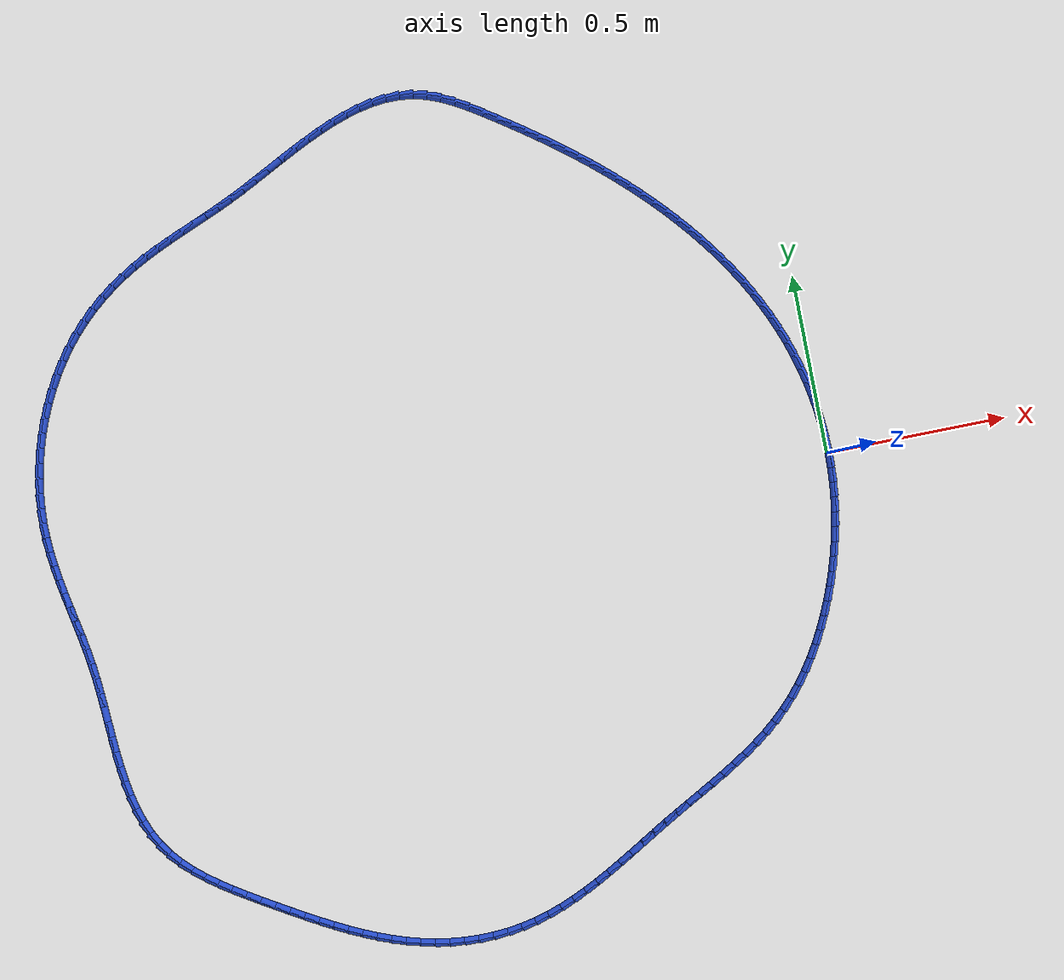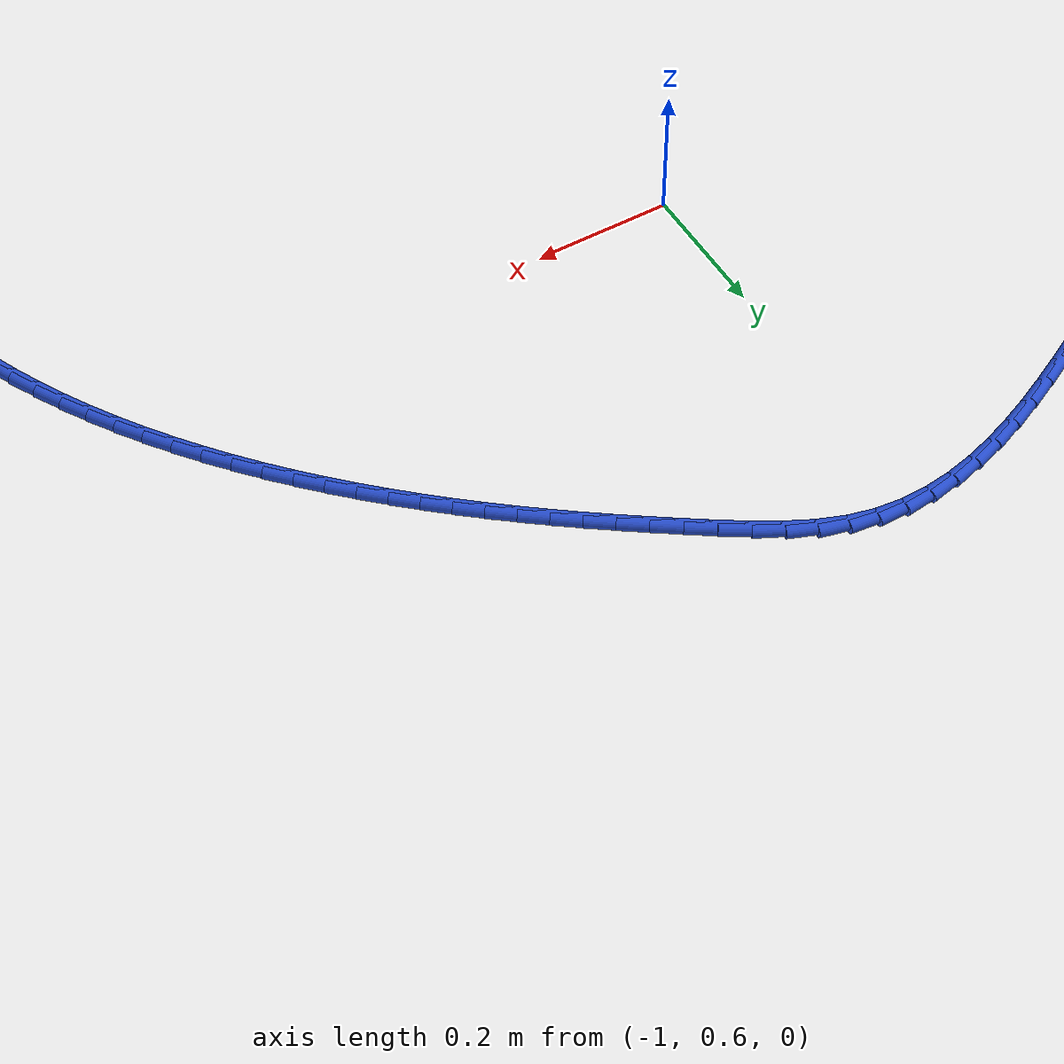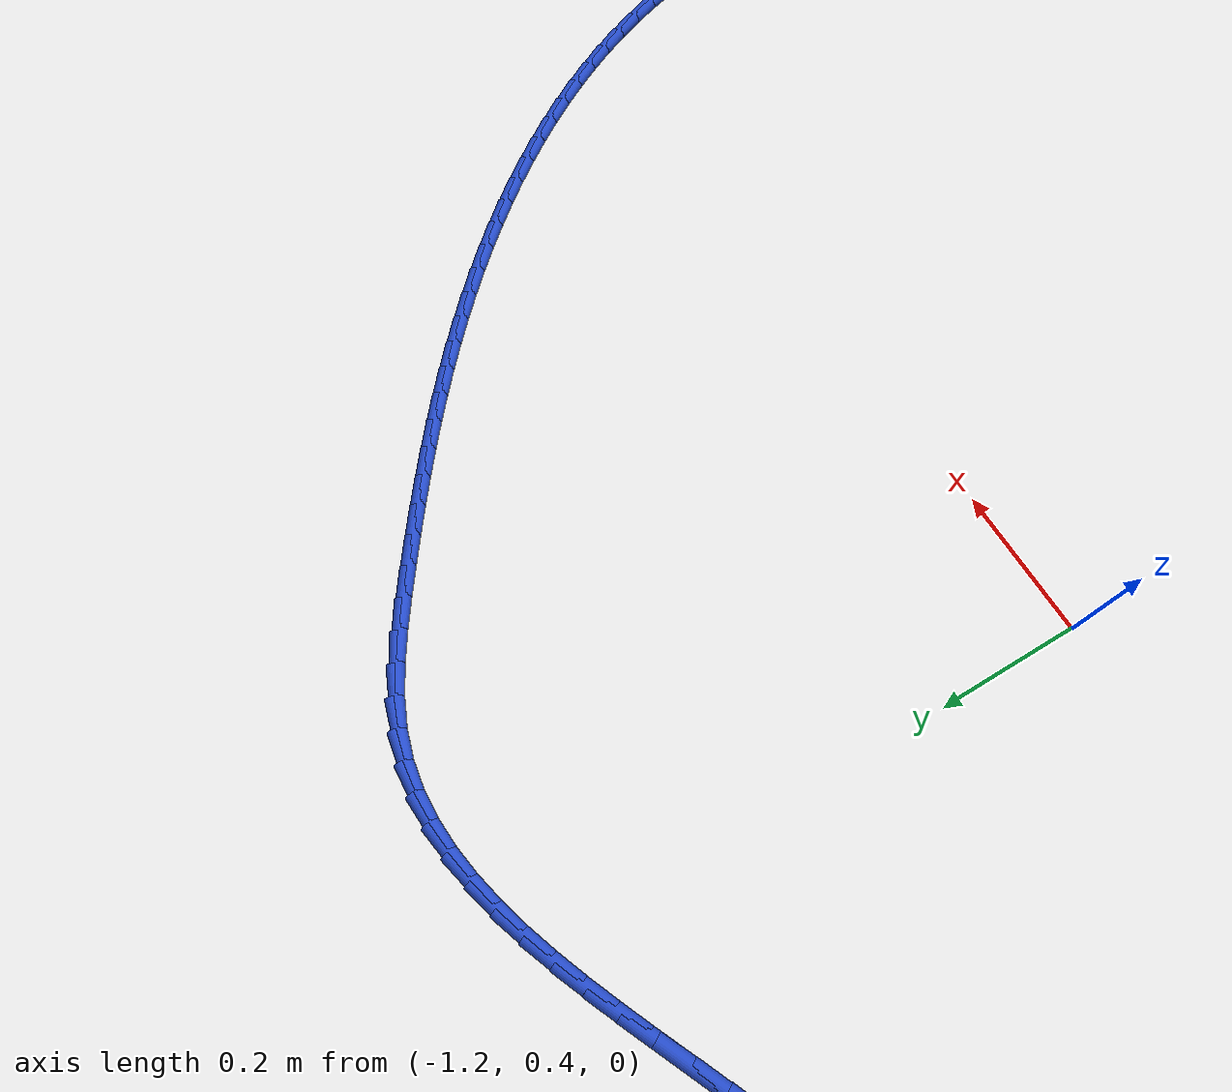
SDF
<sdf version="1.6">
 <world name="default">
  <light name="sun" type="directional">
   <pose>0 0 10 0 -0 0</pose>
   <diffuse>0.8 0.8 0.8 1</diffuse>
   <specular>0.2 0.2 0.2 1</specular>
   <attenuation>
    <range>1000</range>
    <constant>0.9</constant>
    <linear>0.01</linear>
    <quadratic>0.001</quadratic>
   </attenuation>
   <direction>-0.5 0.1 -0.9</direction>
  </light>
  <model name="ground_plane">
   <static>1</static>
   <link name="link">
    <collision name="collision">
     <geometry><plane><normal>0 0 1</normal><size>100 100</size></plane></geometry>
     <surface><friction><ode><mu>100</mu><mu2>50</mu2></ode></friction></surface>
    </collision>
    <visual name="visual">
     <cast_shadows>0</cast_shadows>
     <geometry><plane><normal>0 0 1</normal><size>100 100</size></plane></geometry>
     <material>
      <script><uri>file://media/materials/scripts/gazebo.material</uri><name>Gazebo/WhiteGlow</name></script>
     </material>
    </visual>
   </link>
  </model>
  <gravity>0 0 -9.8</gravity>
  <magnetic_field>6e-06 2.3e-05 -4.2e-05</magnetic_field>
  <atmosphere type="adiabatic"/>
  <physics name="default_physics" default="0" type="ode">
   <max_step_size>0.001</max_step_size>
   <real_time_factor>1</real_time_factor>
   <real_time_update_rate>1000</real_time_update_rate>
  </physics>
  <scene><ambient>0.4 0.4 0.4 1</ambient><background>0.7 0.7 0.7 1</background><shadows>1</shadows></scene>
  <spherical_coordinates>
   <surface_model>EARTH_WGS84</surface_model>
   <latitude_deg>0</latitude_deg>
   <longitude_deg>0</longitude_deg>
   <elevation>0</elevation>
   <heading_deg>0</heading_deg>
  </spherical_coordinates>
  <model name="line">
   <link name="link_0">
    <pose>-1.5612511283791264e-17 -4.163336342344337e-17 0.01 0 1.57 -1.5517195649385054</pose>
    <collision name="collision">
     <geometry><cylinder><radius>0.01</radius><length>0.08</length></cylinder></geometry>
    </collision>
    <visual name="visual">
     <material>
      <script><name>Gazebo/Blue</name><uri>file://media/materials/scripts/gazebo.material</uri></script>
     </material>
     <geometry><cylinder><radius>0.01</radius><length>0.08</length></cylinder></geometry>
    </visual>
   </link>
   <link name="link_1">
    <pose>-0.0007825338649914748 0.041015290816238836 0.01 0 1.57 -1.5096912786628212</pose>
    <collision name="collision">
     <geometry><cylinder><radius>0.01</radius><length>0.08</length></cylinder></geometry>
    </collision>
    <visual name="visual">
     <material>
      <script><name>Gazebo/Blue</name><uri>file://media/materials/scripts/gazebo.material</uri></script>
     </material>
     <geometry><cylinder><radius>0.01</radius><length>0.08</length></cylinder></geometry>
    </visual>
   </link>
   <link name="link_2">
    <pose>-0.0032909838034783775 0.08201562054938584 0.01 0 1.57 -1.4680488592954692</pose>
    <collision name="collision">
     <geometry><cylinder><radius>0.01</radius><length>0.08</length></cylinder></geometry>
    </collision>
    <visual name="visual">
     <material>
      <script><name>Gazebo/Blue</name><uri>file://media/materials/scripts/gazebo.material</uri></script>
     </material>
     <geometry><cylinder><radius>0.01</radius><length>0.08</length></cylinder></geometry>
    </visual>
   </link>
   <link name="link_3">
    <pose>-0.007508788309666879 0.12292126658177949 0.01 0 1.57 -1.4266900710185564</pose>
    <collision name="collision">
     <geometry><cylinder><radius>0.01</radius><length>0.08</length></cylinder></geometry>
    </collision>
    <visual name="visual">
     <material>
      <script><name>Gazebo/Blue</name><uri>file://media/materials/scripts/gazebo.material</uri></script>
     </material>
     <geometry><cylinder><radius>0.01</radius><length>0.08</length></cylinder></geometry>
    </visual>
   </link>
   <link name="link_4">
    <pose>-0.013419385877763135 0.1636525062957585 0.01 0 1.57 -1.385511125466385</pose>
    <collision name="collision">
     <geometry><cylinder><radius>0.01</radius><length>0.08</length></cylinder></geometry>
    </collision>
    <visual name="visual">
     <material>
      <script><name>Gazebo/Blue</name><uri>file://media/materials/scripts/gazebo.material</uri></script>
     </material>
     <geometry><cylinder><radius>0.01</radius><length>0.08</length></cylinder></geometry>
    </visual>
   </link>
   <link name="link_5">
    <pose>-0.021006215001973298 0.20412961707366142 0.01 0 1.57 -1.344407390723362</pose>
    <collision name="collision">
     <geometry><cylinder><radius>0.01</radius><length>0.08</length></cylinder></geometry>
    </collision>
    <visual name="visual">
     <material>
      <script><name>Gazebo/Blue</name><uri>file://media/materials/scripts/gazebo.material</uri></script>
     </material>
     <geometry><cylinder><radius>0.01</radius><length>0.08</length></cylinder></geometry>
    </visual>
   </link>
   <link name="link_6">
    <pose>-0.030252714176503517 0.2442728762978269 0.01 0 1.57 -1.3032740299838046</pose>
    <collision name="collision">
     <geometry><cylinder><radius>0.01</radius><length>0.08</length></cylinder></geometry>
    </collision>
    <visual name="visual">
     <material>
      <script><name>Gazebo/Blue</name><uri>file://media/materials/scripts/gazebo.material</uri></script>
     </material>
     <geometry><cylinder><radius>0.01</radius><length>0.08</length></cylinder></geometry>
    </visual>
   </link>
   <link name="link_7">
    <pose>-0.04114232189555995 0.28400256135059354 0.01 0 1.57 -1.2620066119703555</pose>
    <collision name="collision">
     <geometry><cylinder><radius>0.01</radius><length>0.08</length></cylinder></geometry>
    </collision>
    <visual name="visual">
     <material>
      <script><name>Gazebo/Blue</name><uri>file://media/materials/scripts/gazebo.material</uri></script>
     </material>
     <geometry><cylinder><radius>0.01</radius><length>0.08</length></cylinder></geometry>
    </visual>
   </link>
   <link name="link_8">
    <pose>-0.053658476653348754 0.3232389496142999 0.01 0 1.57 -1.2205017367907247</pose>
    <collision name="collision">
     <geometry><cylinder><radius>0.01</radius><length>0.08</length></cylinder></geometry>
    </collision>
    <visual name="visual">
     <material>
      <script><name>Gazebo/Blue</name><uri>file://media/materials/scripts/gazebo.material</uri></script>
     </material>
     <geometry><cylinder><radius>0.01</radius><length>0.08</length></cylinder></geometry>
    </visual>
   </link>
   <link name="link_9">
    <pose>-0.06778461689388825 0.361902318532766 0.01 0 1.57 -1.1790075497419938</pose>
    <collision name="collision">
     <geometry><cylinder><radius>0.01</radius><length>0.08</length></cylinder></geometry>
    </collision>
    <visual name="visual">
     <material>
      <script><name>Gazebo/Blue</name><uri>file://media/materials/scripts/gazebo.material</uri></script>
     </material>
     <geometry><cylinder><radius>0.01</radius><length>0.08</length></cylinder></geometry>
    </visual>
   </link>
   <link name="link_10">
    <pose>-0.08349384350931358 0.3999256093298315 0.01 0 1.57 -1.1388055713313328</pose>
    <collision name="collision">
     <geometry><cylinder><radius>0.01</radius><length>0.08</length></cylinder></geometry>
    </collision>
    <visual name="visual">
     <material>
      <script><name>Gazebo/Blue</name><uri>file://media/materials/scripts/gazebo.material</uri></script>
     </material>
     <geometry><cylinder><radius>0.01</radius><length>0.08</length></cylinder></geometry>
    </visual>
   </link>
   <link name="link_11">
    <pose>-0.10071998888861775 0.43728986820535826 0.01 0 1.57 -1.100224717903958</pose>
    <collision name="collision">
     <geometry><cylinder><radius>0.01</radius><length>0.08</length></cylinder></geometry>
    </collision>
    <visual name="visual">
     <material>
      <script><name>Gazebo/Blue</name><uri>file://media/materials/scripts/gazebo.material</uri></script>
     </material>
     <geometry><cylinder><radius>0.01</radius><length>0.08</length></cylinder></geometry>
    </visual>
   </link>
   <link name="link_12">
    <pose>-0.1193875627730763 0.47398756185423796 0.01 0 1.57 -1.0632651120558072</pose>
    <collision name="collision">
     <geometry><cylinder><radius>0.01</radius><length>0.08</length></cylinder></geometry>
    </collision>
    <visual name="visual">
     <material>
      <script><name>Gazebo/Blue</name><uri>file://media/materials/scripts/gazebo.material</uri></script>
     </material>
     <geometry><cylinder><radius>0.01</radius><length>0.08</length></cylinder></geometry>
    </visual>
   </link>
   <link name="link_13">
    <pose>-0.13942107490396458 0.5100111569713619 0.01 0 1.57 -1.0279092124318145</pose>
    <collision name="collision">
     <geometry><cylinder><radius>0.01</radius><length>0.08</length></cylinder></geometry>
    </collision>
    <visual name="visual">
     <material>
      <script><name>Gazebo/Blue</name><uri>file://media/materials/scripts/gazebo.material</uri></script>
     </material>
     <geometry><cylinder><radius>0.01</radius><length>0.08</length></cylinder></geometry>
    </visual>
   </link>
   <link name="link_14">
    <pose>-0.16074503502255796 0.5453531202516212 0.01 0 1.57 -0.9941249978693737</pose>
    <collision name="collision">
     <geometry><cylinder><radius>0.01</radius><length>0.08</length></cylinder></geometry>
    </collision>
    <visual name="visual">
     <material>
      <script><name>Gazebo/Blue</name><uri>file://media/materials/scripts/gazebo.material</uri></script>
     </material>
     <geometry><cylinder><radius>0.01</radius><length>0.08</length></cylinder></geometry>
    </visual>
   </link>
   <link name="link_15">
    <pose>-0.18328395287013186 0.5800059183899077 0.01 0 1.57 -0.9618689498673286</pose>
    <collision name="collision">
     <geometry><cylinder><radius>0.01</radius><length>0.08</length></cylinder></geometry>
    </collision>
    <visual name="visual">
     <material>
      <script><name>Gazebo/Blue</name><uri>file://media/materials/scripts/gazebo.material</uri></script>
     </material>
     <geometry><cylinder><radius>0.01</radius><length>0.08</length></cylinder></geometry>
    </visual>
   </link>
   <link name="link_16">
    <pose>-0.20696233818796175 0.6139620180811122 0.01 0 1.57 -0.9310887451572291</pose>
    <collision name="collision">
     <geometry><cylinder><radius>0.01</radius><length>0.08</length></cylinder></geometry>
    </collision>
    <visual name="visual">
     <material>
      <script><name>Gazebo/Blue</name><uri>file://media/materials/scripts/gazebo.material</uri></script>
     </material>
     <geometry><cylinder><radius>0.01</radius><length>0.08</length></cylinder></geometry>
    </visual>
   </link>
   <link name="link_17">
    <pose>-0.231704700717323 0.6472138860201263 0.01 0 1.57 -0.9017256119275018</pose>
    <collision name="collision">
     <geometry><cylinder><radius>0.01</radius><length>0.08</length></cylinder></geometry>
    </collision>
    <visual name="visual">
     <material>
      <script><name>Gazebo/Blue</name><uri>file://media/materials/scripts/gazebo.material</uri></script>
     </material>
     <geometry><cylinder><radius>0.01</radius><length>0.08</length></cylinder></geometry>
    </visual>
   </link>
   <link name="link_18">
    <pose>-0.2574355501994909 0.6797539889018411 0.01 0 1.57 -0.8737163353799792</pose>
    <collision name="collision">
     <geometry><cylinder><radius>0.01</radius><length>0.08</length></cylinder></geometry>
    </collision>
    <visual name="visual">
     <material>
      <script><name>Gazebo/Blue</name><uri>file://media/materials/scripts/gazebo.material</uri></script>
     </material>
     <geometry><cylinder><radius>0.01</radius><length>0.08</length></cylinder></geometry>
    </visual>
   </link>
   <link name="link_19">
    <pose>-0.2840793963757409 0.7115747934211484 0.01 0 1.57 -0.8469949211070643</pose>
    <collision name="collision">
     <geometry><cylinder><radius>0.01</radius><length>0.08</length></cylinder></geometry>
    </collision>
    <visual name="visual">
     <material>
      <script><name>Gazebo/Blue</name><uri>file://media/materials/scripts/gazebo.material</uri></script>
     </material>
     <geometry><cylinder><radius>0.01</radius><length>0.08</length></cylinder></geometry>
    </visual>
   </link>
   <link name="link_20">
    <pose>-0.3115607489873486 0.7426687662729392 0.01 0 1.57 -0.8214939395025926</pose>
    <collision name="collision">
     <geometry><cylinder><radius>0.01</radius><length>0.08</length></cylinder></geometry>
    </collision>
    <visual name="visual">
     <material>
      <script><name>Gazebo/Blue</name><uri>file://media/materials/scripts/gazebo.material</uri></script>
     </material>
     <geometry><cylinder><radius>0.01</radius><length>0.08</length></cylinder></geometry>
    </visual>
   </link>
   <link name="link_21">
    <pose>-0.33980411777558917 0.7730283741521049 0.01 0 1.57 -0.7971455826678787</pose>
    <collision name="collision">
     <geometry><cylinder><radius>0.01</radius><length>0.08</length></cylinder></geometry>
    </collision>
    <visual name="visual">
     <material>
      <script><name>Gazebo/Blue</name><uri>file://media/materials/scripts/gazebo.material</uri></script>
     </material>
     <geometry><cylinder><radius>0.01</radius><length>0.08</length></cylinder></geometry>
    </visual>
   </link>
   <link name="link_22">
    <pose>-0.368734012481738 0.8026460837535367 0.01 0 1.57 -0.77388246867499</pose>
    <collision name="collision">
     <geometry><cylinder><radius>0.01</radius><length>0.08</length></cylinder></geometry>
    </collision>
    <visual name="visual">
     <material>
      <script><name>Gazebo/Blue</name><uri>file://media/materials/scripts/gazebo.material</uri></script>
     </material>
     <geometry><cylinder><radius>0.01</radius><length>0.08</length></cylinder></geometry>
    </visual>
   </link>
   <link name="link_23">
    <pose>-0.3982749428470707 0.8315143617721263 0.01 0 1.57 -0.7516382280463985</pose>
    <collision name="collision">
     <geometry><cylinder><radius>0.01</radius><length>0.08</length></cylinder></geometry>
    </collision>
    <visual name="visual">
     <material>
      <script><name>Gazebo/Blue</name><uri>file://media/materials/scripts/gazebo.material</uri></script>
     </material>
     <geometry><cylinder><radius>0.01</radius><length>0.08</length></cylinder></geometry>
    </visual>
   </link>
   <link name="link_24">
    <pose>-0.4283514186128625 0.8596256749027649 0.01 0 1.57 -0.7303479050788299</pose>
    <collision name="collision">
     <geometry><cylinder><radius>0.01</radius><length>0.08</length></cylinder></geometry>
    </collision>
    <visual name="visual">
     <material>
      <script><name>Gazebo/Blue</name><uri>file://media/materials/scripts/gazebo.material</uri></script>
     </material>
     <geometry><cylinder><radius>0.01</radius><length>0.08</length></cylinder></geometry>
    </visual>
   </link>
   <link name="link_25">
    <pose>-0.4588879495203888 0.8869724898403437 0.01 0 1.57 -0.7099626795273344</pose>
    <collision name="collision">
     <geometry><cylinder><radius>0.01</radius><length>0.08</length></cylinder></geometry>
    </collision>
    <visual name="visual">
     <material>
      <script><name>Gazebo/Blue</name><uri>file://media/materials/scripts/gazebo.material</uri></script>
     </material>
     <geometry><cylinder><radius>0.01</radius><length>0.08</length></cylinder></geometry>
    </visual>
   </link>
   <link name="link_26">
    <pose>-0.4898203367833353 0.9135577561625234 0.01 0 1.57 -0.6905706430932614</pose>
    <collision name="collision">
     <geometry><cylinder><radius>0.01</radius><length>0.08</length></cylinder></geometry>
    </collision>
    <visual name="visual">
     <material>
      <script><name>Gazebo/Blue</name><uri>file://media/materials/scripts/gazebo.material</uri></script>
     </material>
     <geometry><cylinder><radius>0.01</radius><length>0.08</length></cylinder></geometry>
    </visual>
   </link>
   <link name="link_27">
    <pose>-0.5211498620340775 0.9394452147705288 0.01 0 1.57 -0.6723176851539336</pose>
    <collision name="collision">
     <geometry><cylinder><radius>0.01</radius><length>0.08</length></cylinder></geometry>
    </collision>
    <visual name="visual">
     <material>
      <script><name>Gazebo/Blue</name><uri>file://media/materials/scripts/gazebo.material</uri></script>
     </material>
     <geometry><cylinder><radius>0.01</radius><length>0.08</length></cylinder></geometry>
    </visual>
   </link>
   <link name="link_28">
    <pose>-0.552901353123085 0.9647204666237745 0.01 0 1.57 -0.6553197093487563</pose>
    <collision name="collision">
     <geometry><cylinder><radius>0.01</radius><length>0.08</length></cylinder></geometry>
    </collision>
    <visual name="visual">
     <material>
      <script><name>Gazebo/Blue</name><uri>file://media/materials/scripts/gazebo.material</uri></script>
     </material>
     <geometry><cylinder><radius>0.01</radius><length>0.08</length></cylinder></geometry>
    </visual>
   </link>
   <link name="link_29">
    <pose>-0.58509966882472 0.9894691413910883 0.01 0 1.57 -0.6396746259816064</pose>
    <collision name="collision">
     <geometry><cylinder><radius>0.01</radius><length>0.08</length></cylinder></geometry>
    </collision>
    <visual name="visual">
     <material>
      <script><name>Gazebo/Blue</name><uri>file://media/materials/scripts/gazebo.material</uri></script>
     </material>
     <geometry><cylinder><radius>0.01</radius><length>0.08</length></cylinder></geometry>
    </visual>
   </link>
   <link name="link_30">
    <pose>-0.6177696679133462 1.0137768687412994 0.01 0 1.57 -0.6254611918089062</pose>
    <collision name="collision">
     <geometry><cylinder><radius>0.01</radius><length>0.08</length></cylinder></geometry>
    </collision>
    <visual name="visual">
     <material>
      <script><name>Gazebo/Blue</name><uri>file://media/materials/scripts/gazebo.material</uri></script>
     </material>
     <geometry><cylinder><radius>0.01</radius><length>0.08</length></cylinder></geometry>
    </visual>
   </link>
   <link name="link_31">
    <pose>-0.6509362091633265 1.0377292783432353 0.01 0 1.57 -0.6127385009613265</pose>
    <collision name="collision">
     <geometry><cylinder><radius>0.01</radius><length>0.08</length></cylinder></geometry>
    </collision>
    <visual name="visual">
     <material>
      <script><name>Gazebo/Blue</name><uri>file://media/materials/scripts/gazebo.material</uri></script>
     </material>
     <geometry><cylinder><radius>0.01</radius><length>0.08</length></cylinder></geometry>
    </visual>
   </link>
   <link name="link_32">
    <pose>-0.6846241513490241 1.0614119998657245 0.01 0 1.57 -0.6015461071797519</pose>
    <collision name="collision">
     <geometry><cylinder><radius>0.01</radius><length>0.08</length></cylinder></geometry>
    </collision>
    <visual name="visual">
     <material>
      <script><name>Gazebo/Blue</name><uri>file://media/materials/scripts/gazebo.material</uri></script>
     </material>
     <geometry><cylinder><radius>0.01</radius><length>0.08</length></cylinder></geometry>
    </visual>
   </link>
   <link name="link_33">
    <pose>-0.7188583532448021 1.084910662977596 0.01 0 1.57 -0.5916585411646436</pose>
    <collision name="collision">
     <geometry><cylinder><radius>0.01</radius><length>0.08</length></cylinder></geometry>
    </collision>
    <visual name="visual">
     <material>
      <script><name>Gazebo/Blue</name><uri>file://media/materials/scripts/gazebo.material</uri></script>
     </material>
     <geometry><cylinder><radius>0.01</radius><length>0.08</length></cylinder></geometry>
    </visual>
   </link>
   <link name="link_34">
    <pose>-0.7536631852865611 1.1082981315384153 0.01 0 1.57 -0.573368196473278</pose>
    <collision name="collision">
     <geometry><cylinder><radius>0.01</radius><length>0.08</length></cylinder></geometry>
    </collision>
    <visual name="visual">
     <material>
      <script><name>Gazebo/Blue</name><uri>file://media/materials/scripts/gazebo.material</uri></script>
     </material>
     <geometry><cylinder><radius>0.01</radius><length>0.08</length></cylinder></geometry>
    </visual>
   </link>
   <link name="link_35">
    <pose>-0.7890437842172598 1.1311444753942805 0.01 0 1.57 -0.5333619036671445</pose>
    <collision name="collision">
     <geometry><cylinder><radius>0.01</radius><length>0.08</length></cylinder></geometry>
    </collision>
    <visual name="visual">
     <material>
      <script><name>Gazebo/Blue</name><uri>file://media/materials/scripts/gazebo.material</uri></script>
     </material>
     <geometry><cylinder><radius>0.01</radius><length>0.08</length></cylinder></geometry>
    </visual>
   </link>
   <link name="link_36">
    <pose>-0.8249801562062077 1.1523628181655352 0.01 0 1.57 -0.46854795316858827</pose>
    <collision name="collision">
     <geometry><cylinder><radius>0.01</radius><length>0.08</length></cylinder></geometry>
    </collision>
    <visual name="visual">
     <material>
      <script><name>Gazebo/Blue</name><uri>file://media/materials/scripts/gazebo.material</uri></script>
     </material>
     <geometry><cylinder><radius>0.01</radius><length>0.08</length></cylinder></geometry>
    </visual>
   </link>
   <link name="link_37">
    <pose>-0.8614506132054851 1.170821994407329 0.01 0 1.57 -0.3752671056147834</pose>
    <collision name="collision">
     <geometry><cylinder><radius>0.01</radius><length>0.08</length></cylinder></geometry>
    </collision>
    <visual name="visual">
     <material>
      <script><name>Gazebo/Blue</name><uri>file://media/materials/scripts/gazebo.material</uri></script>
     </material>
     <geometry><cylinder><radius>0.01</radius><length>0.08</length></cylinder></geometry>
    </visual>
   </link>
   <link name="link_38">
    <pose>-0.8984334671671717 1.185390838674812 0.01 0 1.57 -0.2518647060923827</pose>
    <collision name="collision">
     <geometry><cylinder><radius>0.01</radius><length>0.08</length></cylinder></geometry>
    </collision>
    <visual name="visual">
     <material>
      <script><name>Gazebo/Blue</name><uri>file://media/materials/scripts/gazebo.material</uri></script>
     </material>
     <geometry><cylinder><radius>0.01</radius><length>0.08</length></cylinder></geometry>
    </visual>
   </link>
   <link name="link_39">
    <pose>-0.9359052928619055 1.195033431868869 0.01 0 1.57 -0.12143163181642301</pose>
    <collision name="collision">
     <geometry><cylinder><radius>0.01</radius><length>0.08</length></cylinder></geometry>
    </collision>
    <visual name="visual">
     <material>
      <script><name>Gazebo/Blue</name><uri>file://media/materials/scripts/gazebo.material</uri></script>
     </material>
     <geometry><cylinder><radius>0.01</radius><length>0.08</length></cylinder></geometry>
    </visual>
   </link>
   <link name="link_40">
    <pose>-0.9738253920925073 1.1996608987767292 0.01 0 1.57 -0.0017251297064345215</pose>
    <collision name="collision">
     <geometry><cylinder><radius>0.01</radius><length>0.08</length></cylinder></geometry>
    </collision>
    <visual name="visual">
     <material>
      <script><name>Gazebo/Blue</name><uri>file://media/materials/scripts/gazebo.material</uri></script>
     </material>
     <geometry><cylinder><radius>0.01</radius><length>0.08</length></cylinder></geometry>
    </visual>
   </link>
   <link name="link_41">
    <pose>-1.0121431695859942 1.1997270019785438 0.01 0 1.57 0.10398435955020283</pose>
    <collision name="collision">
     <geometry><cylinder><radius>0.01</radius><length>0.08</length></cylinder></geometry>
    </collision>
    <visual name="visual">
     <material>
      <script><name>Gazebo/Blue</name><uri>file://media/materials/scripts/gazebo.material</uri></script>
     </material>
     <geometry><cylinder><radius>0.01</radius><length>0.08</length></cylinder></geometry>
    </visual>
   </link>
   <link name="link_42">
    <pose>-1.0508079130600219 1.1956919194545854 0.01 0 1.57 0.19452840680415154</pose>
    <collision name="collision">
     <geometry><cylinder><radius>0.01</radius><length>0.08</length></cylinder></geometry>
    </collision>
    <visual name="visual">
     <material>
      <script><name>Gazebo/Blue</name><uri>file://media/materials/scripts/gazebo.material</uri></script>
     </material>
     <geometry><cylinder><radius>0.01</radius><length>0.08</length></cylinder></geometry>
    </visual>
   </link>
   <link name="link_43">
    <pose>-1.0897689102322456 1.188015829185128 0.01 0 1.57 0.27014667882515564</pose>
    <collision name="collision">
     <geometry><cylinder><radius>0.01</radius><length>0.08</length></cylinder></geometry>
    </collision>
    <visual name="visual">
     <material>
      <script><name>Gazebo/Blue</name><uri>file://media/materials/scripts/gazebo.material</uri></script>
     </material>
     <geometry><cylinder><radius>0.01</radius><length>0.08</length></cylinder></geometry>
    </visual>
   </link>
   <link name="link_44">
    <pose>-1.1289754488203216 1.1771589091504442 0.01 0 1.57 0.33185288801770346</pose>
    <collision name="collision">
     <geometry><cylinder><radius>0.01</radius><length>0.08</length></cylinder></geometry>
    </collision>
    <visual name="visual">
     <material>
      <script><name>Gazebo/Blue</name><uri>file://media/materials/scripts/gazebo.material</uri></script>
     </material>
     <geometry><cylinder><radius>0.01</radius><length>0.08</length></cylinder></geometry>
    </visual>
   </link>
   <link name="link_45">
    <pose>-1.1683768165419062 1.1635813373308075 0.01 0 1.57 0.3809390599780705</pose>
    <collision name="collision">
     <geometry><cylinder><radius>0.01</radius><length>0.08</length></cylinder></geometry>
    </collision>
    <visual name="visual">
     <material>
      <script><name>Gazebo/Blue</name><uri>file://media/materials/scripts/gazebo.material</uri></script>
     </material>
     <geometry><cylinder><radius>0.01</radius><length>0.08</length></cylinder></geometry>
    </visual>
   </link>
   <link name="link_46">
    <pose>-1.2079223011146543 1.1477432917064916 0.01 0 1.57 0.41866784693471476</pose>
    <collision name="collision">
     <geometry><cylinder><radius>0.01</radius><length>0.08</length></cylinder></geometry>
    </collision>
    <visual name="visual">
     <material>
      <script><name>Gazebo/Blue</name><uri>file://media/materials/scripts/gazebo.material</uri></script>
     </material>
     <geometry><cylinder><radius>0.01</radius><length>0.08</length></cylinder></geometry>
    </visual>
   </link>
   <link name="link_47">
    <pose>-1.2475611902562231 1.1301049502577696 0.01 0 1.57 0.4461119407529195</pose>
    <collision name="collision">
     <geometry><cylinder><radius>0.01</radius><length>0.08</length></cylinder></geometry>
    </collision>
    <visual name="visual">
     <material>
      <script><name>Gazebo/Blue</name><uri>file://media/materials/scripts/gazebo.material</uri></script>
     </material>
     <geometry><cylinder><radius>0.01</radius><length>0.08</length></cylinder></geometry>
    </visual>
   </link>
   <link name="link_48">
    <pose>-1.2872427716842665 1.1111264909649146 0.01 0 1.57 0.4640834403702183</pose>
    <collision name="collision">
     <geometry><cylinder><radius>0.01</radius><length>0.08</length></cylinder></geometry>
    </collision>
    <visual name="visual">
     <material>
      <script><name>Gazebo/Blue</name><uri>file://media/materials/scripts/gazebo.material</uri></script>
     </material>
     <geometry><cylinder><radius>0.01</radius><length>0.08</length></cylinder></geometry>
    </visual>
   </link>
   <link name="link_49">
    <pose>-1.3269163331164417 1.0912680918082003 0.01 0 1.57 0.4731088236087587</pose>
    <collision name="collision">
     <geometry><cylinder><radius>0.01</radius><length>0.08</length></cylinder></geometry>
    </collision>
    <visual name="visual">
     <material>
      <script><name>Gazebo/Blue</name><uri>file://media/materials/scripts/gazebo.material</uri></script>
     </material>
     <geometry><cylinder><radius>0.01</radius><length>0.08</length></cylinder></geometry>
    </visual>
   </link>
   <link name="link_50">
    <pose>-1.3665311622704044 1.0709899307678994 0.01 0 1.57 0.47342180470693307</pose>
    <collision name="collision">
     <geometry><cylinder><radius>0.01</radius><length>0.08</length></cylinder></geometry>
    </collision>
    <visual name="visual">
     <material>
      <script><name>Gazebo/Blue</name><uri>file://media/materials/scripts/gazebo.material</uri></script>
     </material>
     <geometry><cylinder><radius>0.01</radius><length>0.08</length></cylinder></geometry>
    </visual>
   </link>
   <link name="link_51">
    <pose>-1.4060365468638103 1.0507521858242859 0.01 0 1.57 0.4649589678113812</pose>
    <collision name="collision">
     <geometry><cylinder><radius>0.01</radius><length>0.08</length></cylinder></geometry>
    </collision>
    <visual name="visual">
     <material>
      <script><name>Gazebo/Blue</name><uri>file://media/materials/scripts/gazebo.material</uri></script>
     </material>
     <geometry><cylinder><radius>0.01</radius><length>0.08</length></cylinder></geometry>
    </visual>
   </link>
   <link name="link_52">
    <pose>-1.4453817746143154 1.0310150349576324 0.01 0 1.57 0.4473514635742701</pose>
    <collision name="collision">
     <geometry><cylinder><radius>0.01</radius><length>0.08</length></cylinder></geometry>
    </collision>
    <visual name="visual">
     <material>
      <script><name>Gazebo/Blue</name><uri>file://media/materials/scripts/gazebo.material</uri></script>
     </material>
     <geometry><cylinder><radius>0.01</radius><length>0.08</length></cylinder></geometry>
    </visual>
   </link>
   <link name="link_53">
    <pose>-1.484516133239575 1.012238656148213 0.01 0 1.57 0.4225645913503844</pose>
    <collision name="collision">
     <geometry><cylinder><radius>0.01</radius><length>0.08</length></cylinder></geometry>
    </collision>
    <visual name="visual">
     <material>
      <script><name>Gazebo/Blue</name><uri>file://media/materials/scripts/gazebo.material</uri></script>
     </material>
     <geometry><cylinder><radius>0.01</radius><length>0.08</length></cylinder></geometry>
    </visual>
   </link>
   <link name="link_54">
    <pose>-1.5233888172710885 0.9947594713552501 0.01 0 1.57 0.4026322766483738</pose>
    <collision name="collision">
     <geometry><cylinder><radius>0.01</radius><length>0.08</length></cylinder></geometry>
    </collision>
    <visual name="visual">
     <material>
      <script><name>Gazebo/Blue</name><uri>file://media/materials/scripts/gazebo.material</uri></script>
     </material>
     <geometry><cylinder><radius>0.01</radius><length>0.08</length></cylinder></geometry>
    </visual>
   </link>
   <link name="link_55">
    <pose>-1.5619485867562162 0.978336885204129 0.01 0 1.57 0.3916602115343521</pose>
    <collision name="collision">
     <geometry><cylinder><radius>0.01</radius><length>0.08</length></cylinder></geometry>
    </collision>
    <visual name="visual">
     <material>
      <script><name>Gazebo/Blue</name><uri>file://media/materials/scripts/gazebo.material</uri></script>
     </material>
     <geometry><cylinder><radius>0.01</radius><length>0.08</length></cylinder></geometry>
    </visual>
   </link>
   <link name="link_56">
    <pose>-1.600144075212409 0.9625622640762735 0.01 0 1.57 0.3901295040325442</pose>
    <collision name="collision">
     <geometry><cylinder><radius>0.01</radius><length>0.08</length></cylinder></geometry>
    </collision>
    <visual name="visual">
     <material>
      <script><name>Gazebo/Blue</name><uri>file://media/materials/scripts/gazebo.material</uri></script>
     </material>
     <geometry><cylinder><radius>0.01</radius><length>0.08</length></cylinder></geometry>
    </visual>
   </link>
   <link name="link_57">
    <pose>-1.6379239161426447 0.9470269551311683 0.01 0 1.57 0.3983855232881524</pose>
    <collision name="collision">
     <geometry><cylinder><radius>0.01</radius><length>0.08</length></cylinder></geometry>
    </collision>
    <visual name="visual">
     <material>
      <script><name>Gazebo/Blue</name><uri>file://media/materials/scripts/gazebo.material</uri></script>
     </material>
     <geometry><cylinder><radius>0.01</radius><length>0.08</length></cylinder></geometry>
    </visual>
   </link>
   <link name="link_58">
    <pose>-1.6752367430498998 0.9313223055282979 0.01 0 1.57 0.41662446041100765</pose>
    <collision name="collision">
     <geometry><cylinder><radius>0.01</radius><length>0.08</length></cylinder></geometry>
    </collision>
    <visual name="visual">
     <material>
      <script><name>Gazebo/Blue</name><uri>file://media/materials/scripts/gazebo.material</uri></script>
     </material>
     <geometry><cylinder><radius>0.01</radius><length>0.08</length></cylinder></geometry>
    </visual>
   </link>
   <link name="link_59">
    <pose>-1.7120311894371512 0.9150396624271475 0.01 0 1.57 0.4448564066520664</pose>
    <collision name="collision">
     <geometry><cylinder><radius>0.01</radius><length>0.08</length></cylinder></geometry>
    </collision>
    <visual name="visual">
     <material>
      <script><name>Gazebo/Blue</name><uri>file://media/materials/scripts/gazebo.material</uri></script>
     </material>
     <geometry><cylinder><radius>0.01</radius><length>0.08</length></cylinder></geometry>
    </visual>
   </link>
   <link name="link_60">
    <pose>-1.748255888807376 0.8977703729872021 0.01 0 1.57 0.4828458462337701</pose>
    <collision name="collision">
     <geometry><cylinder><radius>0.01</radius><length>0.08</length></cylinder></geometry>
    </collision>
    <visual name="visual">
     <material>
      <script><name>Gazebo/Blue</name><uri>file://media/materials/scripts/gazebo.material</uri></script>
     </material>
     <geometry><cylinder><radius>0.01</radius><length>0.08</length></cylinder></geometry>
    </visual>
   </link>
   <link name="link_61">
    <pose>-1.7838594746635525 0.8791057843679462 0.01 0 1.57 0.5296391153219574</pose>
    <collision name="collision">
     <geometry><cylinder><radius>0.01</radius><length>0.08</length></cylinder></geometry>
    </collision>
    <visual name="visual">
     <material>
      <script><name>Gazebo/Blue</name><uri>file://media/materials/scripts/gazebo.material</uri></script>
     </material>
     <geometry><cylinder><radius>0.01</radius><length>0.08</length></cylinder></geometry>
    </visual>
   </link>
   <link name="link_62">
    <pose>-1.8187814134386782 0.8586613520640249 0.01 0 1.57 0.5806577844997015</pose>
    <collision name="collision">
     <geometry><cylinder><radius>0.01</radius><length>0.08</length></cylinder></geometry>
    </collision>
    <visual name="visual">
     <material>
      <script><name>Gazebo/Blue</name><uri>file://media/materials/scripts/gazebo.material</uri></script>
     </material>
     <geometry><cylinder><radius>0.01</radius><length>0.08</length></cylinder></geometry>
    </visual>
   </link>
   <link name="link_63">
    <pose>-1.8528683677417281 0.8362965949075618 0.01 0 1.57 0.6337509216848514</pose>
    <collision name="collision">
     <geometry><cylinder><radius>0.01</radius><length>0.08</length></cylinder></geometry>
    </collision>
    <visual name="visual">
     <material>
      <script><name>Gazebo/Blue</name><uri>file://media/materials/scripts/gazebo.material</uri></script>
     </material>
     <geometry><cylinder><radius>0.01</radius><length>0.08</length></cylinder></geometry>
    </visual>
   </link>
   <link name="link_64">
    <pose>-1.8859130739772367 0.8120128514193801 0.01 0 1.57 0.6892225075739112</pose>
    <collision name="collision">
     <geometry><cylinder><radius>0.01</radius><length>0.08</length></cylinder></geometry>
    </collision>
    <visual name="visual">
     <material>
      <script><name>Gazebo/Blue</name><uri>file://media/materials/scripts/gazebo.material</uri></script>
     </material>
     <geometry><cylinder><radius>0.01</radius><length>0.08</length></cylinder></geometry>
    </visual>
   </link>
   <link name="link_65">
    <pose>-1.9177076028027213 0.7858132109580547 0.01 0 1.57 0.7473666045937405</pose>
    <collision name="collision">
     <geometry><cylinder><radius>0.01</radius><length>0.08</length></cylinder></geometry>
    </collision>
    <visual name="visual">
     <material>
      <script><name>Gazebo/Blue</name><uri>file://media/materials/scripts/gazebo.material</uri></script>
     </material>
     <geometry><cylinder><radius>0.01</radius><length>0.08</length></cylinder></geometry>
    </visual>
   </link>
   <link name="link_66">
    <pose>-1.9480440248756998 0.757700762882161 0.01 0 1.57 0.8083866247125984</pose>
    <collision name="collision">
     <geometry><cylinder><radius>0.01</radius><length>0.08</length></cylinder></geometry>
    </collision>
    <visual name="visual">
     <material>
      <script><name>Gazebo/Blue</name><uri>file://media/materials/scripts/gazebo.material</uri></script>
     </material>
     <geometry><cylinder><radius>0.01</radius><length>0.08</length></cylinder></geometry>
    </visual>
   </link>
   <link name="link_67">
    <pose>-1.97671558155799 0.7276797158193798 0.01 0 1.57 0.8703216692561468</pose>
    <collision name="collision">
     <geometry><cylinder><radius>0.01</radius><length>0.08</length></cylinder></geometry>
    </collision>
    <visual name="visual">
     <material>
      <script><name>Gazebo/Blue</name><uri>file://media/materials/scripts/gazebo.material</uri></script>
     </material>
     <geometry><cylinder><radius>0.01</radius><length>0.08</length></cylinder></geometry>
    </visual>
   </link>
   <link name="link_68">
    <pose>-2.003579967885827 0.6958159002830322 0.01 0 1.57 0.9301552253113292</pose>
    <collision name="collision">
     <geometry><cylinder><radius>0.01</radius><length>0.08</length></cylinder></geometry>
    </collision>
    <visual name="visual">
     <material>
      <script><name>Gazebo/Blue</name><uri>file://media/materials/scripts/gazebo.material</uri></script>
     </material>
     <geometry><cylinder><radius>0.01</radius><length>0.08</length></cylinder></geometry>
    </visual>
   </link>
   <link name="link_69">
    <pose>-2.028591588611781 0.6622676075364928 0.01 0 1.57 0.9878787142149448</pose>
    <collision name="collision">
     <geometry><cylinder><radius>0.01</radius><length>0.08</length></cylinder></geometry>
    </collision>
    <visual name="visual">
     <material>
      <script><name>Gazebo/Blue</name><uri>file://media/materials/scripts/gazebo.material</uri></script>
     </material>
     <geometry><cylinder><radius>0.01</radius><length>0.08</length></cylinder></geometry>
    </visual>
   </link>
   <link name="link_70">
    <pose>-2.0517128052389757 0.6272007360118037 0.01 0 1.57 1.04377891355183</pose>
    <collision name="collision">
     <geometry><cylinder><radius>0.01</radius><length>0.08</length></cylinder></geometry>
    </collision>
    <visual name="visual">
     <material>
      <script><name>Gazebo/Blue</name><uri>file://media/materials/scripts/gazebo.material</uri></script>
     </material>
     <geometry><cylinder><radius>0.01</radius><length>0.08</length></cylinder></geometry>
    </visual>
   </link>
   <link name="link_71">
    <pose>-2.072905979270533 0.5907811841410078 0.01 0 1.57 1.0981628240101502</pose>
    <collision name="collision">
     <geometry><cylinder><radius>0.01</radius><length>0.08</length></cylinder></geometry>
    </collision>
    <visual name="visual">
     <material>
      <script><name>Gazebo/Blue</name><uri>file://media/materials/scripts/gazebo.material</uri></script>
     </material>
     <geometry><cylinder><radius>0.01</radius><length>0.08</length></cylinder></geometry>
    </visual>
   </link>
   <link name="link_72">
    <pose>-2.092133472209577 0.5531748503561486 0.01 0 1.57 1.1513507728124412</pose>
    <collision name="collision">
     <geometry><cylinder><radius>0.01</radius><length>0.08</length></cylinder></geometry>
    </collision>
    <visual name="visual">
     <material>
      <script><name>Gazebo/Blue</name><uri>file://media/materials/scripts/gazebo.material</uri></script>
     </material>
     <geometry><cylinder><radius>0.01</radius><length>0.08</length></cylinder></geometry>
    </visual>
   </link>
   <link name="link_73">
    <pose>-2.10935764555923 0.5145476330892685 0.01 0 1.57 1.203672075323181</pose>
    <collision name="collision">
     <geometry><cylinder><radius>0.01</radius><length>0.08</length></cylinder></geometry>
    </collision>
    <visual name="visual">
     <material>
      <script><name>Gazebo/Blue</name><uri>file://media/materials/scripts/gazebo.material</uri></script>
     </material>
     <geometry><cylinder><radius>0.01</radius><length>0.08</length></cylinder></geometry>
    </visual>
   </link>
   <link name="link_74">
    <pose>-2.1245408608226146 0.4750654307724105 0.01 0 1.57 1.2554627073161793</pose>
    <collision name="collision">
     <geometry><cylinder><radius>0.01</radius><length>0.08</length></cylinder></geometry>
    </collision>
    <visual name="visual">
     <material>
      <script><name>Gazebo/Blue</name><uri>file://media/materials/scripts/gazebo.material</uri></script>
     </material>
     <geometry><cylinder><radius>0.01</radius><length>0.08</length></cylinder></geometry>
    </visual>
   </link>
   <link name="link_75">
    <pose>-2.1376454795028548 0.43489414183761776 0.01 0 1.57 1.3070644568133443</pose>
    <collision name="collision">
     <geometry><cylinder><radius>0.01</radius><length>0.08</length></cylinder></geometry>
    </collision>
    <visual name="visual">
     <material>
      <script><name>Gazebo/Blue</name><uri>file://media/materials/scripts/gazebo.material</uri></script>
     </material>
     <geometry><cylinder><radius>0.01</radius><length>0.08</length></cylinder></geometry>
    </visual>
   </link>
   <link name="link_76">
    <pose>-2.1486338631030732 0.39419966471693313 0.01 0 1.57 1.3588250581907952</pose>
    <collision name="collision">
     <geometry><cylinder><radius>0.01</radius><length>0.08</length></cylinder></geometry>
    </collision>
    <visual name="visual">
     <material>
      <script><name>Gazebo/Blue</name><uri>file://media/materials/scripts/gazebo.material</uri></script>
     </material>
     <geometry><cylinder><radius>0.01</radius><length>0.08</length></cylinder></geometry>
    </visual>
   </link>
   <link name="link_77">
    <pose>-2.1574683731263935 0.35314789784239914 0.01 0 1.57 1.4110988346010285</pose>
    <collision name="collision">
     <geometry><cylinder><radius>0.01</radius><length>0.08</length></cylinder></geometry>
    </collision>
    <visual name="visual">
     <material>
      <script><name>Gazebo/Blue</name><uri>file://media/materials/scripts/gazebo.material</uri></script>
     </material>
     <geometry><cylinder><radius>0.01</radius><length>0.08</length></cylinder></geometry>
    </visual>
   </link>
   <link name="link_78">
    <pose>-2.1641113710759363 0.3119047396460593 0.01 0 1.57 1.4642473699320901</pose>
    <collision name="collision">
     <geometry><cylinder><radius>0.01</radius><length>0.08</length></cylinder></geometry>
    </collision>
    <visual name="visual">
     <material>
      <script><name>Gazebo/Blue</name><uri>file://media/materials/scripts/gazebo.material</uri></script>
     </material>
     <geometry><cylinder><radius>0.01</radius><length>0.08</length></cylinder></geometry>
    </visual>
   </link>
   <link name="link_79">
    <pose>-2.1685252184548274 0.270636088559956 0.01 0 1.57 1.5186396875273767</pose>
    <collision name="collision">
     <geometry><cylinder><radius>0.01</radius><length>0.08</length></cylinder></geometry>
    </collision>
    <visual name="visual">
     <material>
      <script><name>Gazebo/Blue</name><uri>file://media/materials/scripts/gazebo.material</uri></script>
     </material>
     <geometry><cylinder><radius>0.01</radius><length>0.08</length></cylinder></geometry>
    </visual>
   </link>
   <link name="link_80">
    <pose>-2.170672276766189 0.22950784301613292 0.01 0 1.57 -1.5669746648039797</pose>
    <collision name="collision">
     <geometry><cylinder><radius>0.01</radius><length>0.08</length></cylinder></geometry>
    </collision>
    <visual name="visual">
     <material>
      <script><name>Gazebo/Blue</name><uri>file://media/materials/scripts/gazebo.material</uri></script>
     </material>
     <geometry><cylinder><radius>0.01</radius><length>0.08</length></cylinder></geometry>
    </visual>
   </link>
   <link name="link_81">
    <pose>-2.1705162649182945 0.18868500500967827 0.01 0 1.57 -1.512611220973102</pose>
    <collision name="collision">
     <geometry><cylinder><radius>0.01</radius><length>0.08</length></cylinder></geometry>
    </collision>
    <visual name="visual">
     <material>
      <script><name>Gazebo/Blue</name><uri>file://media/materials/scripts/gazebo.material</uri></script>
     </material>
     <geometry><cylinder><radius>0.01</radius><length>0.08</length></cylinder></geometry>
    </visual>
   </link>
   <link name="link_82">
    <pose>-2.1681603374137826 0.14824049259203892 0.01 0 1.57 -1.4667439732891514</pose>
    <collision name="collision">
     <geometry><cylinder><radius>0.01</radius><length>0.08</length></cylinder></geometry>
    </collision>
    <visual name="visual">
     <material>
      <script><name>Gazebo/Blue</name><uri>file://media/materials/scripts/gazebo.material</uri></script>
     </material>
     <geometry><cylinder><radius>0.01</radius><length>0.08</length></cylinder></geometry>
    </visual>
   </link>
   <link name="link_83">
    <pose>-2.1639660398862945 0.10807658105695124 0.01 0 1.57 -1.4306422613213174</pose>
    <collision name="collision">
     <geometry><cylinder><radius>0.01</radius><length>0.08</length></cylinder></geometry>
    </collision>
    <visual name="visual">
     <material>
      <script><name>Gazebo/Blue</name><uri>file://media/materials/scripts/gazebo.material</uri></script>
     </material>
     <geometry><cylinder><radius>0.01</radius><length>0.08</length></cylinder></geometry>
    </visual>
   </link>
   <link name="link_84">
    <pose>-2.1583229433557842 0.06807703759693332 0.01 0 1.57 -1.4045821976316002</pose>
    <collision name="collision">
     <geometry><cylinder><radius>0.01</radius><length>0.08</length></cylinder></geometry>
    </collision>
    <visual name="visual">
     <material>
      <script><name>Gazebo/Blue</name><uri>file://media/materials/scripts/gazebo.material</uri></script>
     </material>
     <geometry><cylinder><radius>0.01</radius><length>0.08</length></cylinder></geometry>
    </visual>
   </link>
   <link name="link_85">
    <pose>-2.1516206188422062 0.02812562940450475 0.01 0 1.57 -1.388628807504665</pose>
    <collision name="collision">
     <geometry><cylinder><radius>0.01</radius><length>0.08</length></cylinder></geometry>
    </collision>
    <visual name="visual">
     <material>
      <script><name>Gazebo/Blue</name><uri>file://media/materials/scripts/gazebo.material</uri></script>
     </material>
     <geometry><cylinder><radius>0.01</radius><length>0.08</length></cylinder></geometry>
    </visual>
   </link>
   <link name="link_86">
    <pose>-2.1442486373655147 -0.011893876327815913 0.01 0 1.57 -1.3827141860553835</pose>
    <collision name="collision">
     <geometry><cylinder><radius>0.01</radius><length>0.08</length></cylinder></geometry>
    </collision>
    <visual name="visual">
     <material>
      <script><name>Gazebo/Blue</name><uri>file://media/materials/scripts/gazebo.material</uri></script>
     </material>
     <geometry><cylinder><radius>0.01</radius><length>0.08</length></cylinder></geometry>
    </visual>
   </link>
   <link name="link_87">
    <pose>-2.1365965699456617 -0.052097712407509864 0.01 0 1.57 -1.386688696020316</pose>
    <collision name="collision">
     <geometry><cylinder><radius>0.01</radius><length>0.08</length></cylinder></geometry>
    </collision>
    <visual name="visual">
     <material>
      <script><name>Gazebo/Blue</name><uri>file://media/materials/scripts/gazebo.material</uri></script>
     </material>
     <geometry><cylinder><radius>0.01</radius><length>0.08</length></cylinder></geometry>
    </visual>
   </link>
   <link name="link_88">
    <pose>-2.129053987602604 -0.09260211164205814 0.01 0 1.57 -1.4003424032719898</pose>
    <collision name="collision">
     <geometry><cylinder><radius>0.01</radius><length>0.08</length></cylinder></geometry>
    </collision>
    <visual name="visual">
     <material>
      <script><name>Gazebo/Blue</name><uri>file://media/materials/scripts/gazebo.material</uri></script>
     </material>
     <geometry><cylinder><radius>0.01</radius><length>0.08</length></cylinder></geometry>
    </visual>
   </link>
   <link name="link_89">
    <pose>-2.122010461356293 -0.13352330683894276 0.01 0 1.57 -1.4233985502641076</pose>
    <collision name="collision">
     <geometry><cylinder><radius>0.01</radius><length>0.08</length></cylinder></geometry>
    </collision>
    <visual name="visual">
     <material>
      <script><name>Gazebo/Blue</name><uri>file://media/materials/scripts/gazebo.material</uri></script>
     </material>
     <geometry><cylinder><radius>0.01</radius><length>0.08</length></cylinder></geometry>
    </visual>
   </link>
   <link name="link_90">
    <pose>-2.1158555622266846 -0.17497753080564318 0.01 0 1.57 -1.4549365931717129</pose>
    <collision name="collision">
     <geometry><cylinder><radius>0.01</radius><length>0.08</length></cylinder></geometry>
    </collision>
    <visual name="visual">
     <material>
      <script><name>Gazebo/Blue</name><uri>file://media/materials/scripts/gazebo.material</uri></script>
     </material>
     <geometry><cylinder><radius>0.01</radius><length>0.08</length></cylinder></geometry>
    </visual>
   </link>
   <link name="link_91">
    <pose>-2.110956618278102 -0.21707156870780195 0.01 0 1.57 -1.484577948276998</pose>
    <collision name="collision">
     <geometry><cylinder><radius>0.01</radius><length>0.08</length></cylinder></geometry>
    </collision>
    <visual name="visual">
     <material>
      <script><name>Gazebo/Blue</name><uri>file://media/materials/scripts/gazebo.material</uri></script>
     </material>
     <geometry><cylinder><radius>0.01</radius><length>0.08</length></cylinder></geometry>
    </visual>
   </link>
   <link name="link_92">
    <pose>-2.1072689152637545 -0.2597371917316656 0.01 0 1.57 -1.5038380625643148</pose>
    <collision name="collision">
     <geometry><cylinder><radius>0.01</radius><length>0.08</length></cylinder></geometry>
    </collision>
    <visual name="visual">
     <material>
      <script><name>Gazebo/Blue</name><uri>file://media/materials/scripts/gazebo.material</uri></script>
     </material>
     <geometry><cylinder><radius>0.01</radius><length>0.08</length></cylinder></geometry>
    </visual>
   </link>
   <link name="link_93">
    <pose>-2.104384416281352 -0.30275185064048804 0.01 0 1.57 -1.5128634796822065</pose>
    <collision name="collision">
     <geometry><cylinder><radius>0.01</radius><length>0.08</length></cylinder></geometry>
    </collision>
    <visual name="visual">
     <material>
      <script><name>Gazebo/Blue</name><uri>file://media/materials/scripts/gazebo.material</uri></script>
     </material>
     <geometry><cylinder><radius>0.01</radius><length>0.08</length></cylinder></geometry>
    </visual>
   </link>
   <link name="link_94">
    <pose>-2.1018826337960066 -0.34588770782130995 0.01 0 1.57 -1.5118454291751737</pose>
    <collision name="collision">
     <geometry><cylinder><radius>0.01</radius><length>0.08</length></cylinder></geometry>
    </collision>
    <visual name="visual">
     <material>
      <script><name>Gazebo/Blue</name><uri>file://media/materials/scripts/gazebo.material</uri></script>
     </material>
     <geometry><cylinder><radius>0.01</radius><length>0.08</length></cylinder></geometry>
    </visual>
   </link>
   <link name="link_95">
    <pose>-2.09934308027283 -0.3889169256611693 0.01 0 1.57 -1.5006963565795994</pose>
    <collision name="collision">
     <geometry><cylinder><radius>0.01</radius><length>0.08</length></cylinder></geometry>
    </collision>
    <visual name="visual">
     <material>
      <script><name>Gazebo/Blue</name><uri>file://media/materials/scripts/gazebo.material</uri></script>
     </material>
     <geometry><cylinder><radius>0.01</radius><length>0.08</length></cylinder></geometry>
    </visual>
   </link>
   <link name="link_96">
    <pose>-2.0963452681769335 -0.43161166654710675 0.01 0 1.57 -1.4790457538364539</pose>
    <collision name="collision">
     <geometry><cylinder><radius>0.01</radius><length>0.08</length></cylinder></geometry>
    </collision>
    <visual name="visual">
     <material>
      <script><name>Gazebo/Blue</name><uri>file://media/materials/scripts/gazebo.material</uri></script>
     </material>
     <geometry><cylinder><radius>0.01</radius><length>0.08</length></cylinder></geometry>
    </visual>
   </link>
   <link name="link_97">
    <pose>-2.0924687099734287 -0.4737440928661618 0.01 0 1.57 -1.4462506267970623</pose>
    <collision name="collision">
     <geometry><cylinder><radius>0.01</radius><length>0.08</length></cylinder></geometry>
    </collision>
    <visual name="visual">
     <material>
      <script><name>Gazebo/Blue</name><uri>file://media/materials/scripts/gazebo.material</uri></script>
     </material>
     <geometry><cylinder><radius>0.01</radius><length>0.08</length></cylinder></geometry>
    </visual>
   </link>
   <link name="link_98">
    <pose>-2.087292918127427 -0.5150863670053745 0.01 0 1.57 -1.401432963454915</pose>
    <collision name="collision">
     <geometry><cylinder><radius>0.01</radius><length>0.08</length></cylinder></geometry>
    </collision>
    <visual name="visual">
     <material>
      <script><name>Gazebo/Blue</name><uri>file://media/materials/scripts/gazebo.material</uri></script>
     </material>
     <geometry><cylinder><radius>0.01</radius><length>0.08</length></cylinder></geometry>
    </visual>
   </link>
   <link name="link_99">
    <pose>-2.0803974051040397 -0.555410651351785 0.01 0 1.57 -1.343569521111235</pose>
    <collision name="collision">
     <geometry><cylinder><radius>0.01</radius><length>0.08</length></cylinder></geometry>
    </collision>
    <visual name="visual">
     <material>
      <script><name>Gazebo/Blue</name><uri>file://media/materials/scripts/gazebo.material</uri></script>
     </material>
     <geometry><cylinder><radius>0.01</radius><length>0.08</length></cylinder></geometry>
    </visual>
   </link>
   <link name="link_100">
    <pose>-2.071361683368379 -0.5944891082924317 0.01 0 1.57 -1.2716728883143111</pose>
    <collision name="collision">
     <geometry><cylinder><radius>0.01</radius><length>0.08</length></cylinder></geometry>
    </collision>
    <visual name="visual">
     <material>
      <script><name>Gazebo/Blue</name><uri>file://media/materials/scripts/gazebo.material</uri></script>
     </material>
     <geometry><cylinder><radius>0.01</radius><length>0.08</length></cylinder></geometry>
    </visual>
   </link>
   <link name="link_101">
    <pose>-2.0597652653855554 -0.6320939002143549 0.01 0 1.57 -1.1851075467900452</pose>
    <collision name="collision">
     <geometry><cylinder><radius>0.01</radius><length>0.08</length></cylinder></geometry>
    </collision>
    <visual name="visual">
     <material>
      <script><name>Gazebo/Blue</name><uri>file://media/materials/scripts/gazebo.material</uri></script>
     </material>
     <geometry><cylinder><radius>0.01</radius><length>0.08</length></cylinder></geometry>
    </visual>
   </link>
   <link name="link_102">
    <pose>-2.0451876636206814 -0.6679971895045945 0.01 0 1.57 -1.0840565536095168</pose>
    <collision name="collision">
     <geometry><cylinder><radius>0.01</radius><length>0.08</length></cylinder></geometry>
    </collision>
    <visual name="visual">
     <material>
      <script><name>Gazebo/Blue</name><uri>file://media/materials/scripts/gazebo.material</uri></script>
     </material>
     <geometry><cylinder><radius>0.01</radius><length>0.08</length></cylinder></geometry>
    </visual>
   </link>
   <link name="link_103">
    <pose>-2.0272083905388687 -0.7019711385501901 0.01 0 1.57 -0.9711878049467965</pose>
    <collision name="collision">
     <geometry><cylinder><radius>0.01</radius><length>0.08</length></cylinder></geometry>
    </collision>
    <visual name="visual">
     <material>
      <script><name>Gazebo/Blue</name><uri>file://media/materials/scripts/gazebo.material</uri></script>
     </material>
     <geometry><cylinder><radius>0.01</radius><length>0.08</length></cylinder></geometry>
    </visual>
   </link>
   <link name="link_104">
    <pose>-2.0054460209244778 -0.7338078431716478 0.01 0 1.57 -0.8640282366280053</pose>
    <collision name="collision">
     <geometry><cylinder><radius>0.01</radius><length>0.08</length></cylinder></geometry>
    </collision>
    <visual name="visual">
     <material>
      <script><name>Gazebo/Blue</name><uri>file://media/materials/scripts/gazebo.material</uri></script>
     </material>
     <geometry><cylinder><radius>0.01</radius><length>0.08</length></cylinder></geometry>
    </visual>
   </link>
   <link name="link_105">
    <pose>-1.9800368540178983 -0.7635635930774826 0.01 0 1.57 -0.77416474549689</pose>
    <collision name="collision">
     <geometry><cylinder><radius>0.01</radius><length>0.08</length></cylinder></geometry>
    </collision>
    <visual name="visual">
     <material>
      <script><name>Gazebo/Blue</name><uri>file://media/materials/scripts/gazebo.material</uri></script>
     </material>
     <geometry><cylinder><radius>0.01</radius><length>0.08</length></cylinder></geometry>
    </visual>
   </link>
   <link name="link_106">
    <pose>-1.9514841300766068 -0.7914819273380054 0.01 0 1.57 -0.7011515112616201</pose>
    <collision name="collision">
     <geometry><cylinder><radius>0.01</radius><length>0.08</length></cylinder></geometry>
    </collision>
    <visual name="visual">
     <material>
      <script><name>Gazebo/Blue</name><uri>file://media/materials/scripts/gazebo.material</uri></script>
     </material>
     <geometry><cylinder><radius>0.01</radius><length>0.08</length></cylinder></geometry>
    </visual>
   </link>
   <link name="link_107">
    <pose>-1.9202988702500876 -0.8178103555991634 0.01 0 1.57 -0.6436154490286321</pose>
    <collision name="collision">
     <geometry><cylinder><radius>0.01</radius><length>0.08</length></cylinder></geometry>
    </collision>
    <visual name="visual">
     <material>
      <script><name>Gazebo/Blue</name><uri>file://media/materials/scripts/gazebo.material</uri></script>
     </material>
     <geometry><cylinder><radius>0.01</radius><length>0.08</length></cylinder></geometry>
    </visual>
   </link>
   <link name="link_108">
    <pose>-1.8869920956878266 -0.8427963875069038 0.01 0 1.57 -0.600057680319079</pose>
    <collision name="collision">
     <geometry><cylinder><radius>0.01</radius><length>0.08</length></cylinder></geometry>
    </collision>
    <visual name="visual">
     <material>
      <script><name>Gazebo/Blue</name><uri>file://media/materials/scripts/gazebo.material</uri></script>
     </material>
     <geometry><cylinder><radius>0.01</radius><length>0.08</length></cylinder></geometry>
    </visual>
   </link>
   <link name="link_109">
    <pose>-1.852074827539309 -0.8666875327071744 0.01 0 1.57 -0.5691763671136789</pose>
    <collision name="collision">
     <geometry><cylinder><radius>0.01</radius><length>0.08</length></cylinder></geometry>
    </collision>
    <visual name="visual">
     <material>
      <script><name>Gazebo/Blue</name><uri>file://media/materials/scripts/gazebo.material</uri></script>
     </material>
     <geometry><cylinder><radius>0.01</radius><length>0.08</length></cylinder></geometry>
    </visual>
   </link>
   <link name="link_110">
    <pose>-1.81605808695402 -0.8897313008459227 0.01 0 1.57 -0.5500211801570817</pose>
    <collision name="collision">
     <geometry><cylinder><radius>0.01</radius><length>0.08</length></cylinder></geometry>
    </collision>
    <visual name="visual">
     <material>
      <script><name>Gazebo/Blue</name><uri>file://media/materials/scripts/gazebo.material</uri></script>
     </material>
     <geometry><cylinder><radius>0.01</radius><length>0.08</length></cylinder></geometry>
    </visual>
   </link>
   <link name="link_111">
    <pose>-1.7794528950814448 -0.9121752015690949 0.01 0 1.57 -0.5417710768865921</pose>
    <collision name="collision">
     <geometry><cylinder><radius>0.01</radius><length>0.08</length></cylinder></geometry>
    </collision>
    <visual name="visual">
     <material>
      <script><name>Gazebo/Blue</name><uri>file://media/materials/scripts/gazebo.material</uri></script>
     </material>
     <geometry><cylinder><radius>0.01</radius><length>0.08</length></cylinder></geometry>
    </visual>
   </link>
   <link name="link_112">
    <pose>-1.742759284182877 -0.9342588710385372 0.01 0 1.57 -0.5370126611332768</pose>
    <collision name="collision">
     <geometry><cylinder><radius>0.01</radius><length>0.08</length></cylinder></geometry>
    </collision>
    <visual name="visual">
     <material>
      <script><name>Gazebo/Blue</name><uri>file://media/materials/scripts/gazebo.material</uri></script>
     </material>
     <geometry><cylinder><radius>0.01</radius><length>0.08</length></cylinder></geometry>
    </visual>
   </link>
   <link name="link_113">
    <pose>-1.706201620029016 -0.9560244317374427 0.01 0 1.57 -0.5280489884835077</pose>
    <collision name="collision">
     <geometry><cylinder><radius>0.01</radius><length>0.08</length></cylinder></geometry>
    </collision>
    <visual name="visual">
     <material>
      <script><name>Gazebo/Blue</name><uri>file://media/materials/scripts/gazebo.material</uri></script>
     </material>
     <geometry><cylinder><radius>0.01</radius><length>0.08</length></cylinder></geometry>
    </visual>
   </link>
   <link name="link_114">
    <pose>-1.6697152320489788 -0.9773069130381693 0.01 0 1.57 -0.5144078990532482</pose>
    <collision name="collision">
     <geometry><cylinder><radius>0.01</radius><length>0.08</length></cylinder></geometry>
    </collision>
    <visual name="visual">
     <material>
      <script><name>Gazebo/Blue</name><uri>file://media/materials/scripts/gazebo.material</uri></script>
     </material>
     <geometry><cylinder><radius>0.01</radius><length>0.08</length></cylinder></geometry>
    </visual>
   </link>
   <link name="link_115">
    <pose>-1.633221784933153 -0.9979315535952831 0.01 0 1.57 -0.4959681884255443</pose>
    <collision name="collision">
     <geometry><cylinder><radius>0.01</radius><length>0.08</length></cylinder></geometry>
    </collision>
    <visual name="visual">
     <material>
      <script><name>Gazebo/Blue</name><uri>file://media/materials/scripts/gazebo.material</uri></script>
     </material>
     <geometry><cylinder><radius>0.01</radius><length>0.08</length></cylinder></geometry>
    </visual>
   </link>
   <link name="link_116">
    <pose>-1.596642943371927 -1.0177235920633476 0.01 0 1.57 -0.4726078155521831</pose>
    <collision name="collision">
     <geometry><cylinder><radius>0.01</radius><length>0.08</length></cylinder></geometry>
    </collision>
    <visual name="visual">
     <material>
      <script><name>Gazebo/Blue</name><uri>file://media/materials/scripts/gazebo.material</uri></script>
     </material>
     <geometry><cylinder><radius>0.01</radius><length>0.08</length></cylinder></geometry>
    </visual>
   </link>
   <link name="link_117">
    <pose>-1.5599003720556883 -1.0365082670969292 0.01 0 1.57 -0.4442168294046933</pose>
    <collision name="collision">
     <geometry><cylinder><radius>0.01</radius><length>0.08</length></cylinder></geometry>
    </collision>
    <visual name="visual">
     <material>
      <script><name>Gazebo/Blue</name><uri>file://media/materials/scripts/gazebo.material</uri></script>
     </material>
     <geometry><cylinder><radius>0.01</radius><length>0.08</length></cylinder></geometry>
    </visual>
   </link>
   <link name="link_118">
    <pose>-1.5229157356748244 -1.0541108173505935 0.01 0 1.57 -0.4107152126682764</pose>
    <collision name="collision">
     <geometry><cylinder><radius>0.01</radius><length>0.08</length></cylinder></geometry>
    </collision>
    <visual name="visual">
     <material>
      <script><name>Gazebo/Blue</name><uri>file://media/materials/scripts/gazebo.material</uri></script>
     </material>
     <geometry><cylinder><radius>0.01</radius><length>0.08</length></cylinder></geometry>
    </visual>
   </link>
   <link name="link_119">
    <pose>-1.4856106989197235 -1.0703564814789053 0.01 0 1.57 -0.3720758002350325</pose>
    <collision name="collision">
     <geometry><cylinder><radius>0.01</radius><length>0.08</length></cylinder></geometry>
    </collision>
    <visual name="visual">
     <material>
      <script><name>Gazebo/Blue</name><uri>file://media/materials/scripts/gazebo.material</uri></script>
     </material>
     <geometry><cylinder><radius>0.01</radius><length>0.08</length></cylinder></geometry>
    </visual>
   </link>
   <link name="link_120">
    <pose>-1.4479069264807733 -1.08507049813643 0.01 0 1.57 -0.328351628093782</pose>
    <collision name="collision">
     <geometry><cylinder><radius>0.01</radius><length>0.08</length></cylinder></geometry>
    </collision>
    <visual name="visual">
     <material>
      <script><name>Gazebo/Blue</name><uri>file://media/materials/scripts/gazebo.material</uri></script>
     </material>
     <geometry><cylinder><radius>0.01</radius><length>0.08</length></cylinder></geometry>
    </visual>
   </link>
   <link name="link_121">
    <pose>-1.409726083048361 -1.0980781059777334 0.01 0 1.57 -0.27970577591454315</pose>
    <collision name="collision">
     <geometry><cylinder><radius>0.01</radius><length>0.08</length></cylinder></geometry>
    </collision>
    <visual name="visual">
     <material>
      <script><name>Gazebo/Blue</name><uri>file://media/materials/scripts/gazebo.material</uri></script>
     </material>
     <geometry><cylinder><radius>0.01</radius><length>0.08</length></cylinder></geometry>
    </visual>
   </link>
   <link name="link_122">
    <pose>-1.3709898333128754 -1.10920454365738 0.01 0 1.57 -0.22644006120271212</pose>
    <collision name="collision">
     <geometry><cylinder><radius>0.01</radius><length>0.08</length></cylinder></geometry>
    </collision>
    <visual name="visual">
     <material>
      <script><name>Gazebo/Blue</name><uri>file://media/materials/scripts/gazebo.material</uri></script>
     </material>
     <geometry><cylinder><radius>0.01</radius><length>0.08</length></cylinder></geometry>
    </visual>
   </link>
   <link name="link_123">
    <pose>-1.3316198419647043 -1.1182750498299359 0.01 0 1.57 -0.16902413854825532</pose>
    <collision name="collision">
     <geometry><cylinder><radius>0.01</radius><length>0.08</length></cylinder></geometry>
    </collision>
    <visual name="visual">
     <material>
      <script><name>Gazebo/Blue</name><uri>file://media/materials/scripts/gazebo.material</uri></script>
     </material>
     <geometry><cylinder><radius>0.01</radius><length>0.08</length></cylinder></geometry>
    </visual>
   </link>
   <link name="link_124">
    <pose>-1.2915383764967538 -1.1251150470598854 0.01 0 1.57 -0.10919733554889177</pose>
    <collision name="collision">
     <geometry><cylinder><radius>0.01</radius><length>0.08</length></cylinder></geometry>
    </collision>
    <visual name="visual">
     <material>
      <script><name>Gazebo/Blue</name><uri>file://media/materials/scripts/gazebo.material</uri></script>
     </material>
     <geometry><cylinder><radius>0.01</radius><length>0.08</length></cylinder></geometry>
    </visual>
   </link>
   <link name="link_125">
    <pose>-1.2507783357051103 -1.1295837105810267 0.01 0 1.57 -0.04925684979870692</pose>
    <collision name="collision">
     <geometry><cylinder><radius>0.01</radius><length>0.08</length></cylinder></geometry>
    </collision>
    <visual name="visual">
     <material>
      <script><name>Gazebo/Blue</name><uri>file://media/materials/scripts/gazebo.material</uri></script>
     </material>
     <geometry><cylinder><radius>0.01</radius><length>0.08</length></cylinder></geometry>
    </visual>
   </link>
   <link name="link_126">
    <pose>-1.2096115123455111 -1.1316131001416578 0.01 0 1.57 0.011347221105103928</pose>
    <collision name="collision">
     <geometry><cylinder><radius>0.01</radius><length>0.08</length></cylinder></geometry>
    </collision>
    <visual name="visual">
     <material>
      <script><name>Gazebo/Blue</name><uri>file://media/materials/scripts/gazebo.material</uri></script>
     </material>
     <geometry><cylinder><radius>0.01</radius><length>0.08</length></cylinder></geometry>
    </visual>
   </link>
   <link name="link_127">
    <pose>-1.1683408274226084 -1.1311447724539712 0.01 0 1.57 0.07350668223300093</pose>
    <collision name="collision">
     <geometry><cylinder><radius>0.01</radius><length>0.08</length></cylinder></geometry>
    </collision>
    <visual name="visual">
     <material>
      <script><name>Gazebo/Blue</name><uri>file://media/materials/scripts/gazebo.material</uri></script>
     </material>
     <geometry><cylinder><radius>0.01</radius><length>0.08</length></cylinder></geometry>
    </visual>
   </link>
   <link name="link_128">
    <pose>-1.1272692019410513 -1.1281202842301594 0.01 0 1.57 0.13811288753462334</pose>
    <collision name="collision">
     <geometry><cylinder><radius>0.01</radius><length>0.08</length></cylinder></geometry>
    </collision>
    <visual name="visual">
     <material>
      <script><name>Gazebo/Blue</name><uri>file://media/materials/scripts/gazebo.material</uri></script>
     </material>
     <geometry><cylinder><radius>0.01</radius><length>0.08</length></cylinder></geometry>
    </visual>
   </link>
   <link name="link_129">
    <pose>-1.086699556905491 -1.1224811921824147 0.01 0 1.57 0.2053468417369336</pose>
    <collision name="collision">
     <geometry><cylinder><radius>0.01</radius><length>0.08</length></cylinder></geometry>
    </collision>
    <visual name="visual">
     <material>
      <script><name>Gazebo/Blue</name><uri>file://media/materials/scripts/gazebo.material</uri></script>
     </material>
     <geometry><cylinder><radius>0.01</radius><length>0.08</length></cylinder></geometry>
    </visual>
   </link>
   <link name="link_130">
    <pose>-1.0469056558449064 -1.114192811849778 0.01 0 1.57 0.2695636979742183</pose>
    <collision name="collision">
     <geometry><cylinder><radius>0.01</radius><length>0.08</length></cylinder></geometry>
    </collision>
    <visual name="visual">
     <material>
      <script><name>Gazebo/Blue</name><uri>file://media/materials/scripts/gazebo.material</uri></script>
     </material>
     <geometry><cylinder><radius>0.01</radius><length>0.08</length></cylinder></geometry>
    </visual>
   </link>
   <link name="link_131">
    <pose>-1.0079158993122173 -1.103420391595695 0.01 0 1.57 0.3271736164402615</pose>
    <collision name="collision">
     <geometry><cylinder><radius>0.01</radius><length>0.08</length></cylinder></geometry>
    </collision>
    <visual name="visual">
     <material>
      <script><name>Gazebo/Blue</name><uri>file://media/materials/scripts/gazebo.material</uri></script>
     </material>
     <geometry><cylinder><radius>0.01</radius><length>0.08</length></cylinder></geometry>
    </visual>
   </link>
   <link name="link_132">
    <pose>-0.9696358323666775 -1.09042928798346 0.01 0 1.57 0.3776968937336899</pose>
    <collision name="collision">
     <geometry><cylinder><radius>0.01</radius><length>0.08</length></cylinder></geometry>
    </collision>
    <visual name="visual">
     <material>
      <script><name>Gazebo/Blue</name><uri>file://media/materials/scripts/gazebo.material</uri></script>
     </material>
     <geometry><cylinder><radius>0.01</radius><length>0.08</length></cylinder></geometry>
    </visual>
   </link>
   <link name="link_133">
    <pose>-0.9319700841347781 -1.0754856039197094 0.01 0 1.57 0.4209292623758609</pose>
    <collision name="collision">
     <geometry><cylinder><radius>0.01</radius><length>0.08</length></cylinder></geometry>
    </collision>
    <visual name="visual">
     <material>
      <script><name>Gazebo/Blue</name><uri>file://media/materials/scripts/gazebo.material</uri></script>
     </material>
     <geometry><cylinder><radius>0.01</radius><length>0.08</length></cylinder></geometry>
    </visual>
   </link>
   <link name="link_134">
    <pose>-0.8948232837430098 -1.0588554423110799 0.01 0 1.57 0.45684802586626283</pose>
    <collision name="collision">
     <geometry><cylinder><radius>0.01</radius><length>0.08</length></cylinder></geometry>
    </collision>
    <visual name="visual">
     <material>
      <script><name>Gazebo/Blue</name><uri>file://media/materials/scripts/gazebo.material</uri></script>
     </material>
     <geometry><cylinder><radius>0.01</radius><length>0.08</length></cylinder></geometry>
    </visual>
   </link>
   <link name="link_135">
    <pose>-0.8581000603178638 -1.0408049060642082 0.01 0 1.57 0.4855431480776303</pose>
    <collision name="collision">
     <geometry><cylinder><radius>0.01</radius><length>0.08</length></cylinder></geometry>
    </collision>
    <visual name="visual">
     <material>
      <script><name>Gazebo/Blue</name><uri>file://media/materials/scripts/gazebo.material</uri></script>
     </material>
     <geometry><cylinder><radius>0.01</radius><length>0.08</length></cylinder></geometry>
    </visual>
   </link>
   <link name="link_136">
    <pose>-0.8217050429858312 -1.021600098085731 0.01 0 1.57 0.5071592679019236</pose>
    <collision name="collision">
     <geometry><cylinder><radius>0.01</radius><length>0.08</length></cylinder></geometry>
    </collision>
    <visual name="visual">
     <material>
      <script><name>Gazebo/Blue</name><uri>file://media/materials/scripts/gazebo.material</uri></script>
     </material>
     <geometry><cylinder><radius>0.01</radius><length>0.08</length></cylinder></geometry>
    </visual>
   </link>
   <link name="link_137">
    <pose>-0.7855428608734046 -1.0015071212822861 0.01 0 1.57 0.5218515947433531</pose>
    <collision name="collision">
     <geometry><cylinder><radius>0.01</radius><length>0.08</length></cylinder></geometry>
    </collision>
    <visual name="visual">
     <material>
      <script><name>Gazebo/Blue</name><uri>file://media/materials/scripts/gazebo.material</uri></script>
     </material>
     <geometry><cylinder><radius>0.01</radius><length>0.08</length></cylinder></geometry>
    </visual>
   </link>
   <link name="link_138">
    <pose>-0.7495181431070744 -0.9807920785605095 0.01 0 1.57 0.5297552996347948</pose>
    <collision name="collision">
     <geometry><cylinder><radius>0.01</radius><length>0.08</length></cylinder></geometry>
    </collision>
    <visual name="visual">
     <material>
      <script><name>Gazebo/Blue</name><uri>file://media/materials/scripts/gazebo.material</uri></script>
     </material>
     <geometry><cylinder><radius>0.01</radius><length>0.08</length></cylinder></geometry>
    </visual>
   </link>
   <link name="link_139">
    <pose>-0.7135355188133324 -0.9597210728270387 0.01 0 1.57 0.5309666258725403</pose>
    <collision name="collision">
     <geometry><cylinder><radius>0.01</radius><length>0.08</length></cylinder></geometry>
    </collision>
    <visual name="visual">
     <material>
      <script><name>Gazebo/Blue</name><uri>file://media/materials/scripts/gazebo.material</uri></script>
     </material>
     <geometry><cylinder><radius>0.01</radius><length>0.08</length></cylinder></geometry>
    </visual>
   </link>
   <link name="link_140">
    <pose>-0.6774996171186694 -0.9385602069885096 0.01 0 1.57 0.5255338315294927</pose>
    <collision name="collision">
     <geometry><cylinder><radius>0.01</radius><length>0.08</length></cylinder></geometry>
    </collision>
    <visual name="visual">
     <material>
      <script><name>Gazebo/Blue</name><uri>file://media/materials/scripts/gazebo.material</uri></script>
     </material>
     <geometry><cylinder><radius>0.01</radius><length>0.08</length></cylinder></geometry>
    </visual>
   </link>
   <link name="link_141">
    <pose>-0.6413150671495769 -0.91757558395156 0.01 0 1.57 0.5138970835920944</pose>
    <collision name="collision">
     <geometry><cylinder><radius>0.01</radius><length>0.08</length></cylinder></geometry>
    </collision>
    <visual name="visual">
     <material>
      <script><name>Gazebo/Blue</name><uri>file://media/materials/scripts/gazebo.material</uri></script>
     </material>
     <geometry><cylinder><radius>0.01</radius><length>0.08</length></cylinder></geometry>
    </visual>
   </link>
   <link name="link_142">
    <pose>-0.6048954848321562 -0.8970172275635997 0.01 0 1.57 0.5033015829899977</pose>
    <collision name="collision">
     <geometry><cylinder><radius>0.01</radius><length>0.08</length></cylinder></geometry>
    </collision>
    <visual name="visual">
     <material>
      <script><name>Gazebo/Blue</name><uri>file://media/materials/scripts/gazebo.material</uri></script>
     </material>
     <geometry><cylinder><radius>0.01</radius><length>0.08</length></cylinder></geometry>
    </visual>
   </link>
   <link name="link_143">
    <pose>-0.5683029717995735 -0.8768694930712576 0.01 0 1.57 0.49971337136199684</pose>
    <collision name="collision">
     <geometry><cylinder><radius>0.01</radius><length>0.08</length></cylinder></geometry>
    </collision>
    <visual name="visual">
     <material>
      <script><name>Gazebo/Blue</name><uri>file://media/materials/scripts/gazebo.material</uri></script>
     </material>
     <geometry><cylinder><radius>0.01</radius><length>0.08</length></cylinder></geometry>
    </visual>
   </link>
   <link name="link_144">
    <pose>-0.5317215559312365 -0.8568985869452338 0.01 0 1.57 0.5033464887339731</pose>
    <collision name="collision">
     <geometry><cylinder><radius>0.01</radius><length>0.08</length></cylinder></geometry>
    </collision>
    <visual name="visual">
     <material>
      <script><name>Gazebo/Blue</name><uri>file://media/materials/scripts/gazebo.material</uri></script>
     </material>
     <geometry><cylinder><radius>0.01</radius><length>0.08</length></cylinder></geometry>
    </visual>
   </link>
   <link name="link_145">
    <pose>-0.4953388752596892 -0.8368642564195071 0.01 0 1.57 0.5142885204646499</pose>
    <collision name="collision">
     <geometry><cylinder><radius>0.01</radius><length>0.08</length></cylinder></geometry>
    </collision>
    <visual name="visual">
     <material>
      <script><name>Gazebo/Blue</name><uri>file://media/materials/scripts/gazebo.material</uri></script>
     </material>
     <geometry><cylinder><radius>0.01</radius><length>0.08</length></cylinder></geometry>
    </visual>
   </link>
   <link name="link_146">
    <pose>-0.4593425678174746 -0.8165262487280557 0.01 0 1.57 0.5326734865781435</pose>
    <collision name="collision">
     <geometry><cylinder><radius>0.01</radius><length>0.08</length></cylinder></geometry>
    </collision>
    <visual name="visual">
     <material>
      <script><name>Gazebo/Blue</name><uri>file://media/materials/scripts/gazebo.material</uri></script>
     </material>
     <geometry><cylinder><radius>0.01</radius><length>0.08</length></cylinder></geometry>
    </visual>
   </link>
   <link name="link_147">
    <pose>-0.4239202716371355 -0.7956443111048568 0.01 0 1.57 0.5586660349636073</pose>
    <collision name="collision">
     <geometry><cylinder><radius>0.01</radius><length>0.08</length></cylinder></geometry>
    </collision>
    <visual name="visual">
     <material>
      <script><name>Gazebo/Blue</name><uri>file://media/materials/scripts/gazebo.material</uri></script>
     </material>
     <geometry><cylinder><radius>0.01</radius><length>0.08</length></cylinder></geometry>
    </visual>
   </link>
   <link name="link_148">
    <pose>-0.38925962475121656 -0.7739781907838896 0.01 0 1.57 0.5924317961222765</pose>
    <collision name="collision">
     <geometry><cylinder><radius>0.01</radius><length>0.08</length></cylinder></geometry>
    </collision>
    <visual name="visual">
     <material>
      <script><name>Gazebo/Blue</name><uri>file://media/materials/scripts/gazebo.material</uri></script>
     </material>
     <geometry><cylinder><radius>0.01</radius><length>0.08</length></cylinder></geometry>
    </visual>
   </link>
   <link name="link_149">
    <pose>-0.35554826519226057 -0.751287634999132 0.01 0 1.57 0.6340915433228768</pose>
    <collision name="collision">
     <geometry><cylinder><radius>0.01</radius><length>0.08</length></cylinder></geometry>
    </collision>
    <visual name="visual">
     <material>
      <script><name>Gazebo/Blue</name><uri>file://media/materials/scripts/gazebo.material</uri></script>
     </material>
     <geometry><cylinder><radius>0.01</radius><length>0.08</length></cylinder></geometry>
    </visual>
   </link>
   <link name="link_150">
    <pose>-0.3229738309928109 -0.7273323909845618 0.01 0 1.57 0.6836579091171162</pose>
    <collision name="collision">
     <geometry><cylinder><radius>0.01</radius><length>0.08</length></cylinder></geometry>
    </collision>
    <visual name="visual">
     <material>
      <script><name>Gazebo/Blue</name><uri>file://media/materials/scripts/gazebo.material</uri></script>
     </material>
     <geometry><cylinder><radius>0.01</radius><length>0.08</length></cylinder></geometry>
    </visual>
   </link>
   <link name="link_151">
    <pose>-0.29172396018541086 -0.7018722059741573 0.01 0 1.57 0.7409568600808863</pose>
    <collision name="collision">
     <geometry><cylinder><radius>0.01</radius><length>0.08</length></cylinder></geometry>
    </collision>
    <visual name="visual">
     <material>
      <script><name>Gazebo/Blue</name><uri>file://media/materials/scripts/gazebo.material</uri></script>
     </material>
     <geometry><cylinder><radius>0.01</radius><length>0.08</length></cylinder></geometry>
    </visual>
   </link>
   <link name="link_152">
    <pose>-0.26198629080260377 -0.6746668272018966 0.01 0 1.57 0.8038977202169142</pose>
    <collision name="collision">
     <geometry><cylinder><radius>0.01</radius><length>0.08</length></cylinder></geometry>
    </collision>
    <visual name="visual">
     <material>
      <script><name>Gazebo/Blue</name><uri>file://media/materials/scripts/gazebo.material</uri></script>
     </material>
     <geometry><cylinder><radius>0.01</radius><length>0.08</length></cylinder></geometry>
    </visual>
   </link>
   <link name="link_153">
    <pose>-0.23391651163135171 -0.645538793107977 0.01 0 1.57 0.8647896317328125</pose>
    <collision name="collision">
     <geometry><cylinder><radius>0.01</radius><length>0.08</length></cylinder></geometry>
    </collision>
    <visual name="visual">
     <material>
      <script><name>Gazebo/Blue</name><uri>file://media/materials/scripts/gazebo.material</uri></script>
     </material>
     <geometry><cylinder><radius>0.01</radius><length>0.08</length></cylinder></geometry>
    </visual>
   </link>
   <link name="link_154">
    <pose>-0.2075285905597992 -0.6145891722205992 0.01 0 1.57 0.9216897400848567</pose>
    <collision name="collision">
     <geometry><cylinder><radius>0.01</radius><length>0.08</length></cylinder></geometry>
    </collision>
    <visual name="visual">
     <material>
      <script><name>Gazebo/Blue</name><uri>file://media/materials/scripts/gazebo.material</uri></script>
     </material>
     <geometry><cylinder><radius>0.01</radius><length>0.08</length></cylinder></geometry>
    </visual>
   </link>
   <link name="link_155">
    <pose>-0.1827972131833558 -0.5819962362224956 0.01 0 1.57 0.9748107311259483</pose>
    <collision name="collision">
     <geometry><cylinder><radius>0.01</radius><length>0.08</length></cylinder></geometry>
    </collision>
    <visual name="visual">
     <material>
      <script><name>Gazebo/Blue</name><uri>file://media/materials/scripts/gazebo.material</uri></script>
     </material>
     <geometry><cylinder><radius>0.01</radius><length>0.08</length></cylinder></geometry>
    </visual>
   </link>
   <link name="link_156">
    <pose>-0.15969706364650163 -0.5479382596479735 0.01 0 1.57 1.0244195104598022</pose>
    <collision name="collision">
     <geometry><cylinder><radius>0.01</radius><length>0.08</length></cylinder></geometry>
    </collision>
    <visual name="visual">
     <material>
      <script><name>Gazebo/Blue</name><uri>file://media/materials/scripts/gazebo.material</uri></script>
     </material>
     <geometry><cylinder><radius>0.01</radius><length>0.08</length></cylinder></geometry>
    </visual>
   </link>
   <link name="link_157">
    <pose>-0.13820282609371679 -0.5125935170313403 0.01 0 1.57 1.0708143091091191</pose>
    <collision name="collision">
     <geometry><cylinder><radius>0.01</radius><length>0.08</length></cylinder></geometry>
    </collision>
    <visual name="visual">
     <material>
      <script><name>Gazebo/Blue</name><uri>file://media/materials/scripts/gazebo.material</uri></script>
     </material>
     <geometry><cylinder><radius>0.01</radius><length>0.08</length></cylinder></geometry>
    </visual>
   </link>
   <link name="link_158">
    <pose>-0.11828918466948084 -0.476140282906902 0.01 0 1.57 1.1143080790687372</pose>
    <collision name="collision">
     <geometry><cylinder><radius>0.01</radius><length>0.08</length></cylinder></geometry>
    </collision>
    <visual name="visual">
     <material>
      <script><name>Gazebo/Blue</name><uri>file://media/materials/scripts/gazebo.material</uri></script>
     </material>
     <geometry><cylinder><radius>0.01</radius><length>0.08</length></cylinder></geometry>
    </visual>
   </link>
   <link name="link_159">
    <pose>-0.09993082351827466 -0.43875683180896785 0.01 0 1.57 1.1552173468384601</pose>
    <collision name="collision">
     <geometry><cylinder><radius>0.01</radius><length>0.08</length></cylinder></geometry>
    </collision>
    <visual name="visual">
     <material>
      <script><name>Gazebo/Blue</name><uri>file://media/materials/scripts/gazebo.material</uri></script>
     </material>
     <geometry><cylinder><radius>0.01</radius><length>0.08</length></cylinder></geometry>
    </visual>
   </link>
   <link name="link_160">
    <pose>-0.08310242678457784 -0.4006214382718442 0.01 0 1.57 1.1938555353087463</pose>
    <collision name="collision">
     <geometry><cylinder><radius>0.01</radius><length>0.08</length></cylinder></geometry>
    </collision>
    <visual name="visual">
     <material>
      <script><name>Gazebo/Blue</name><uri>file://media/materials/scripts/gazebo.material</uri></script>
     </material>
     <geometry><cylinder><radius>0.01</radius><length>0.08</length></cylinder></geometry>
    </visual>
   </link>
   <link name="link_161">
    <pose>-0.06777867861287042 -0.36191237682983807 0.01 0 1.57 1.230906622281904</pose>
    <collision name="collision">
     <geometry><cylinder><radius>0.01</radius><length>0.08</length></cylinder></geometry>
    </collision>
    <visual name="visual">
     <material>
      <script><name>Gazebo/Blue</name><uri>file://media/materials/scripts/gazebo.material</uri></script>
     </material>
     <geometry><cylinder><radius>0.01</radius><length>0.08</length></cylinder></geometry>
    </visual>
   </link>
   <link name="link_162">
    <pose>-0.053942910277183655 -0.32278548753776737 0.01 0 1.57 1.2681542247756987</pose>
    <collision name="collision">
     <geometry><cylinder><radius>0.01</radius><length>0.08</length></cylinder></geometry>
    </collision>
    <visual name="visual">
     <material>
      <script><name>Gazebo/Blue</name><uri>file://media/materials/scripts/gazebo.material</uri></script>
     </material>
     <geometry><cylinder><radius>0.01</radius><length>0.08</length></cylinder></geometry>
    </visual>
   </link>
   <link name="link_163">
    <pose>-0.04161487616268959 -0.283302112786803 0.01 0 1.57 1.3060535093180632</pose>
    <collision name="collision">
     <geometry><cylinder><radius>0.01</radius><length>0.08</length></cylinder></geometry>
    </collision>
    <visual name="visual">
     <material>
      <script><name>Gazebo/Blue</name><uri>file://media/materials/scripts/gazebo.material</uri></script>
     </material>
     <geometry><cylinder><radius>0.01</radius><length>0.08</length></cylinder></geometry>
    </visual>
   </link>
   <link name="link_164">
    <pose>-0.030823919148418415 -0.24349871817316424 0.01 0 1.57 1.3446204081305912</pose>
    <collision name="collision">
     <geometry><cylinder><radius>0.01</radius><length>0.08</length></cylinder></geometry>
    </collision>
    <visual name="visual">
     <material>
      <script><name>Gazebo/Blue</name><uri>file://media/materials/scripts/gazebo.material</uri></script>
     </material>
     <geometry><cylinder><radius>0.01</radius><length>0.08</length></cylinder></geometry>
    </visual>
   </link>
   <link name="link_165">
    <pose>-0.02159938215995084 -0.20341176917229414 0.01 0 1.57 1.383864687800172</pose>
    <collision name="collision">
     <geometry><cylinder><radius>0.01</radius><length>0.08</length></cylinder></geometry>
    </collision>
    <visual name="visual">
     <material>
      <script><name>Gazebo/Blue</name><uri>file://media/materials/scripts/gazebo.material</uri></script>
     </material>
     <geometry><cylinder><radius>0.01</radius><length>0.08</length></cylinder></geometry>
    </visual>
   </link>
   <link name="link_166">
    <pose>-0.013970608122867795 -0.1630777312596363 0.01 0 1.57 1.423789128653216</pose>
    <collision name="collision">
     <geometry><cylinder><radius>0.01</radius><length>0.08</length></cylinder></geometry>
    </collision>
    <visual name="visual">
     <material>
      <script><name>Gazebo/Blue</name><uri>file://media/materials/scripts/gazebo.material</uri></script>
     </material>
     <geometry><cylinder><radius>0.01</radius><length>0.08</length></cylinder></geometry>
    </visual>
   </link>
   <link name="link_167">
    <pose>-0.007966939962750254 -0.12253306991063442 0.01 0 1.57 1.4643887188677502</pose>
    <collision name="collision">
     <geometry><cylinder><radius>0.01</radius><length>0.08</length></cylinder></geometry>
    </collision>
    <visual name="visual">
     <material>
      <script><name>Gazebo/Blue</name><uri>file://media/materials/scripts/gazebo.material</uri></script>
     </material>
     <geometry><cylinder><radius>0.01</radius><length>0.08</length></cylinder></geometry>
    </visual>
   </link>
   <link name="link_168">
    <pose>-0.0036177206051790723 -0.08181425060073133 0.01 0 1.57 1.5056498984095952</pose>
    <collision name="collision">
     <geometry><cylinder><radius>0.01</radius><length>0.08</length></cylinder></geometry>
    </collision>
    <visual name="visual">
     <material>
      <script><name>Gazebo/Blue</name><uri>file://media/materials/scripts/gazebo.material</uri></script>
     </material>
     <geometry><cylinder><radius>0.01</radius><length>0.08</length></cylinder></geometry>
    </visual>
   </link>
   <link name="link_169">
    <pose>-0.0009522929757353783 -0.04095773880537224 0.01 0 1.57 1.5475498913556804</pose>
    <collision name="collision">
     <geometry><cylinder><radius>0.01</radius><length>0.08</length></cylinder></geometry>
    </collision>
    <visual name="visual">
     <material>
      <script><name>Gazebo/Blue</name><uri>file://media/materials/scripts/gazebo.material</uri></script>
     </material>
     <geometry><cylinder><radius>0.01</radius><length>0.08</length></cylinder></geometry>
    </visual>
   </link>
   <link name="link_170">
    <pose>-1.5612511283791264e-17 -1.3877787807814457e-17 0.01 0 1.57 -1.551536484257412</pose>
    <collision name="collision">
     <geometry><cylinder><radius>0.01</radius><length>0.08</length></cylinder></geometry>
    </collision>
    <visual name="visual">
     <material>
      <script><name>Gazebo/Blue</name><uri>file://media/materials/scripts/gazebo.material</uri></script>
     </material>
     <geometry><cylinder><radius>0.01</radius><length>0.08</length></cylinder></geometry>
    </visual>
   </link>
   <link name="link_171">
    <pose>-0.0007901846035539371 0.04102250033994168 0.01 0 1.57 -1.551536484257412</pose>
    <collision name="collision">
     <geometry><cylinder><radius>0.01</radius><length>0.08</length></cylinder></geometry>
    </collision>
    <visual name="visual">
     <material>
      <script><name>Gazebo/Blue</name><uri>file://media/materials/scripts/gazebo.material</uri></script>
     </material>
     <geometry><cylinder><radius>0.01</radius><length>0.08</length></cylinder></geometry>
    </visual>
   </link>
  </model>
 </world>
</sdf>
